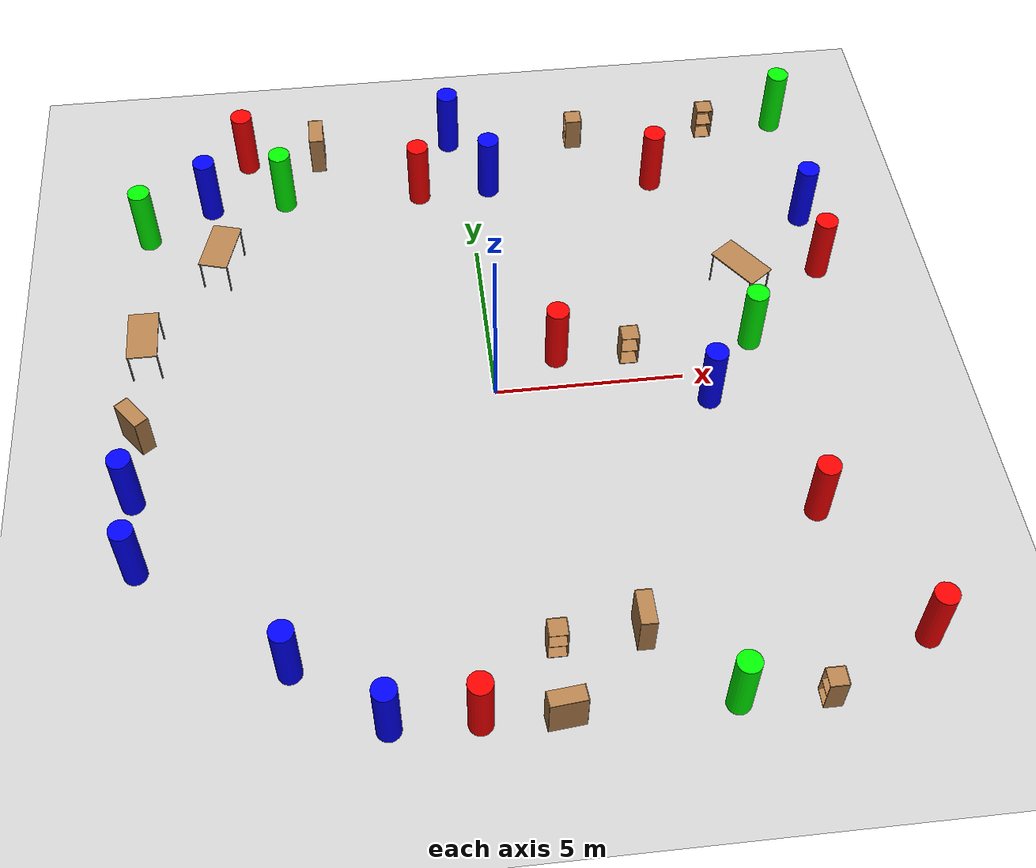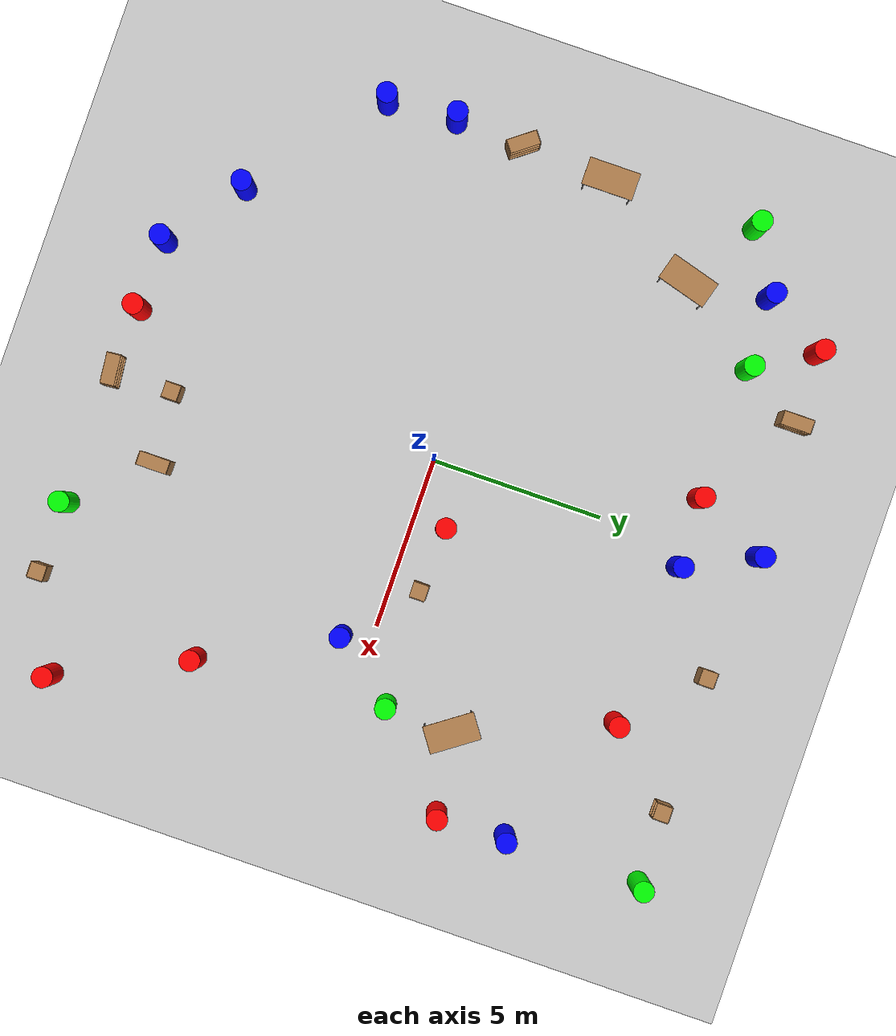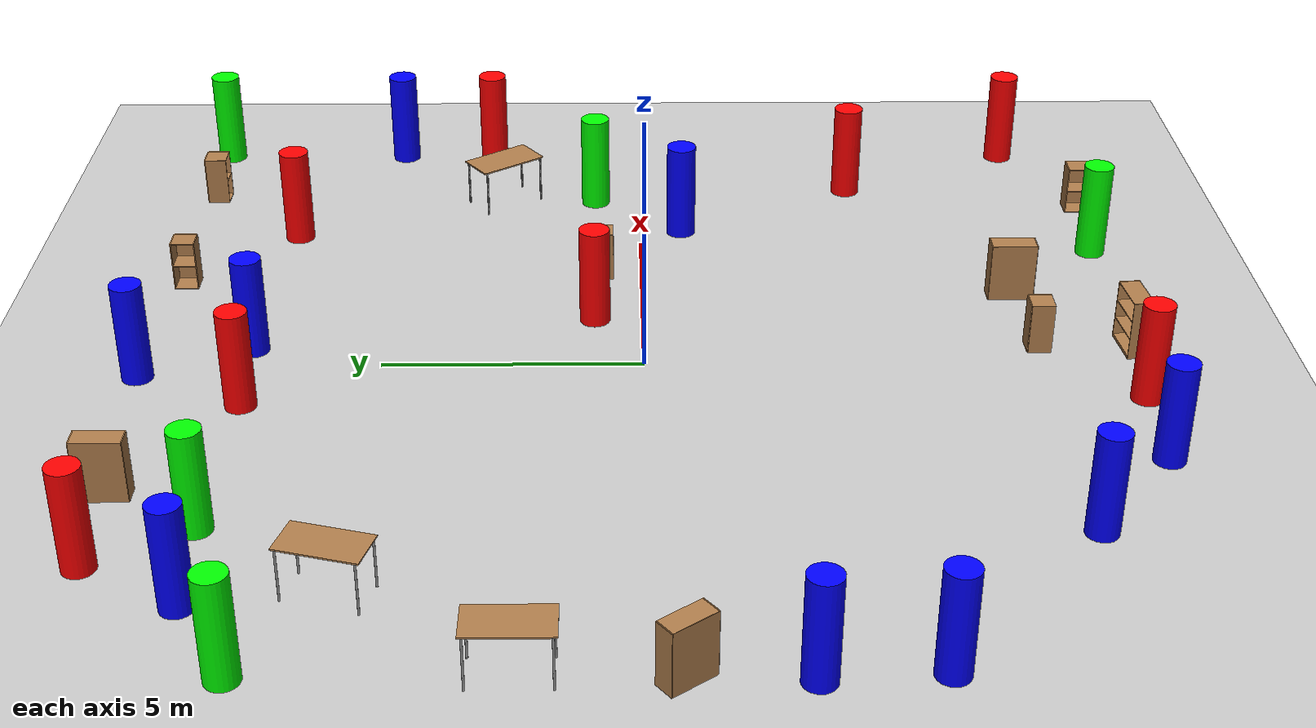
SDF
<sdf version="1.6">
 <world name="default">
  <light name="sun" type="directional">
   <pose>0 0 10 0 -0 0</pose>
   <diffuse>0.8 0.8 0.8 1</diffuse>
   <specular>0.2 0.2 0.2 1</specular>
   <attenuation>
    <range>1000</range>
    <constant>0.9</constant>
    <linear>0.01</linear>
    <quadratic>0.001</quadratic>
   </attenuation>
   <direction>-0.5 0.1 -0.9</direction>
  </light>
  <model name="ground_plane">
   <static>1</static>
   <link name="link">
    <collision name="collision">
     <geometry><plane><normal>0 0 1</normal><size>100 100</size></plane></geometry>
     <surface>
      <contact><collide_bitmask>65535</collide_bitmask></contact>
      <friction><ode><mu>100</mu><mu2>50</mu2></ode></friction>
     </surface>
    </collision>
    <visual name="visual">
     <cast_shadows>0</cast_shadows>
     <geometry><plane><normal>0 0 1</normal><size>100 100</size></plane></geometry>
     <material>
      <script><uri>file://media/materials/scripts/gazebo.material</uri><name>Gazebo/Grey</name></script>
     </material>
    </visual>
   </link>
  </model>
  <gravity>0 0 -9.8</gravity>
  <magnetic_field>6e-06 2.3e-05 -4.2e-05</magnetic_field>
  <atmosphere type="adiabatic"/>
  <physics name="default_physics" default="0" type="ode">
   <max_step_size>0.001</max_step_size>
   <real_time_factor>1</real_time_factor>
   <real_time_update_rate>1000</real_time_update_rate>
  </physics>
  <scene><ambient>0.4 0.4 0.4 1</ambient><background>0.7 0.7 0.7 1</background><shadows>0</shadows></scene>
  <audio><device>default</device></audio>
  <spherical_coordinates>
   <surface_model>EARTH_WGS84</surface_model>
   <latitude_deg>0</latitude_deg>
   <longitude_deg>0</longitude_deg>
   <elevation>0</elevation>
   <heading_deg>0</heading_deg>
  </spherical_coordinates>
  <model name="bookshelf0">
   <static>1</static>
   <link name="link">
    <inertial><mass>1</mass></inertial>
    <collision name="back">
     <pose>0 0.005 0.6 0 -0 0</pose>
     <geometry><box><size>0.9 0.01 1.2</size></box></geometry>
    </collision>
    <visual name="visual1">
     <pose>0 0.005 0.6 0 -0 0</pose>
     <geometry><box><size>0.9 0.01 1.2</size></box></geometry>
     <material>
      <script><uri>file://media/materials/scripts/gazebo.material</uri><name>Gazebo/Wood</name></script>
     </material>
    </visual>
    <collision name="left_side">
     <pose>0.45 -0.195 0.6 0 -0 0</pose>
     <geometry><box><size>0.02 0.4 1.2</size></box></geometry>
    </collision>
    <visual name="visual2">
     <pose>0.45 -0.195 0.6 0 -0 0</pose>
     <geometry><box><size>0.02 0.4 1.2</size></box></geometry>
     <material>
      <script><uri>file://media/materials/scripts/gazebo.material</uri><name>Gazebo/Wood</name></script>
     </material>
    </visual>
    <collision name="right_side">
     <pose>-0.45 -0.195 0.6 0 -0 0</pose>
     <geometry><box><size>0.02 0.4 1.2</size></box></geometry>
    </collision>
    <visual name="visual3">
     <pose>-0.45 -0.195 0.6 0 -0 0</pose>
     <geometry><box><size>0.02 0.4 1.2</size></box></geometry>
     <material>
      <script><uri>file://media/materials/scripts/gazebo.material</uri><name>Gazebo/Wood</name></script>
     </material>
    </visual>
    <collision name="bottom">
     <pose>0 -0.195 0.03 0 -0 0</pose>
     <geometry><box><size>0.88 0.4 0.06</size></box></geometry>
    </collision>
    <visual name="visual4">
     <pose>0 -0.195 0.03 0 -0 0</pose>
     <geometry><box><size>0.88 0.4 0.06</size></box></geometry>
     <material>
      <script><uri>file://media/materials/scripts/gazebo.material</uri><name>Gazebo/Wood</name></script>
     </material>
    </visual>
    <collision name="top">
     <pose>0 -0.195 1.19 0 -0 0</pose>
     <geometry><box><size>0.88 0.4 0.02</size></box></geometry>
    </collision>
    <visual name="visual5">
     <pose>0 -0.195 1.19 0 -0 0</pose>
     <geometry><box><size>0.88 0.4 0.02</size></box></geometry>
     <material>
      <script><uri>file://media/materials/scripts/gazebo.material</uri><name>Gazebo/Wood</name></script>
     </material>
    </visual>
    <collision name="low_shelf">
     <pose>0 -0.195 0.43 0 -0 0</pose>
     <geometry><box><size>0.88 0.4 0.02</size></box></geometry>
    </collision>
    <visual name="visual6">
     <pose>0 -0.195 0.43 0 -0 0</pose>
     <geometry><box><size>0.88 0.4 0.02</size></box></geometry>
     <material>
      <script><uri>file://media/materials/scripts/gazebo.material</uri><name>Gazebo/Wood</name></script>
     </material>
    </visual>
    <collision name="high_shelf">
     <pose>0 -0.195 0.8 0 -0 0</pose>
     <geometry><box><size>0.88 0.4 0.02</size></box></geometry>
    </collision>
    <visual name="visual7">
     <pose>0 -0.195 0.8 0 -0 0</pose>
     <geometry><box><size>0.88 0.4 0.02</size></box></geometry>
     <material>
      <script><uri>file://media/materials/scripts/gazebo.material</uri><name>Gazebo/Wood</name></script>
     </material>
    </visual>
   </link>
   <pose>-9.41642 -0.664219 0 0 -0 2.221</pose>
  </model>
  <model name="bookshelf3">
   <static>1</static>
   <link name="link">
    <inertial><mass>1</mass></inertial>
    <collision name="back">
     <pose>0 0.005 0.6 0 -0 0</pose>
     <geometry><box><size>0.9 0.01 1.2</size></box></geometry>
    </collision>
    <visual name="visual1">
     <pose>0 0.005 0.6 0 -0 0</pose>
     <geometry><box><size>0.9 0.01 1.2</size></box></geometry>
     <material>
      <script><uri>file://media/materials/scripts/gazebo.material</uri><name>Gazebo/Wood</name></script>
     </material>
    </visual>
    <collision name="left_side">
     <pose>0.45 -0.195 0.6 0 -0 0</pose>
     <geometry><box><size>0.02 0.4 1.2</size></box></geometry>
    </collision>
    <visual name="visual2">
     <pose>0.45 -0.195 0.6 0 -0 0</pose>
     <geometry><box><size>0.02 0.4 1.2</size></box></geometry>
     <material>
      <script><uri>file://media/materials/scripts/gazebo.material</uri><name>Gazebo/Wood</name></script>
     </material>
    </visual>
    <collision name="right_side">
     <pose>-0.45 -0.195 0.6 0 -0 0</pose>
     <geometry><box><size>0.02 0.4 1.2</size></box></geometry>
    </collision>
    <visual name="visual3">
     <pose>-0.45 -0.195 0.6 0 -0 0</pose>
     <geometry><box><size>0.02 0.4 1.2</size></box></geometry>
     <material>
      <script><uri>file://media/materials/scripts/gazebo.material</uri><name>Gazebo/Wood</name></script>
     </material>
    </visual>
    <collision name="bottom">
     <pose>0 -0.195 0.03 0 -0 0</pose>
     <geometry><box><size>0.88 0.4 0.06</size></box></geometry>
    </collision>
    <visual name="visual4">
     <pose>0 -0.195 0.03 0 -0 0</pose>
     <geometry><box><size>0.88 0.4 0.06</size></box></geometry>
     <material>
      <script><uri>file://media/materials/scripts/gazebo.material</uri><name>Gazebo/Wood</name></script>
     </material>
    </visual>
    <collision name="top">
     <pose>0 -0.195 1.19 0 -0 0</pose>
     <geometry><box><size>0.88 0.4 0.02</size></box></geometry>
    </collision>
    <visual name="visual5">
     <pose>0 -0.195 1.19 0 -0 0</pose>
     <geometry><box><size>0.88 0.4 0.02</size></box></geometry>
     <material>
      <script><uri>file://media/materials/scripts/gazebo.material</uri><name>Gazebo/Wood</name></script>
     </material>
    </visual>
    <collision name="low_shelf">
     <pose>0 -0.195 0.43 0 -0 0</pose>
     <geometry><box><size>0.88 0.4 0.02</size></box></geometry>
    </collision>
    <visual name="visual6">
     <pose>0 -0.195 0.43 0 -0 0</pose>
     <geometry><box><size>0.88 0.4 0.02</size></box></geometry>
     <material>
      <script><uri>file://media/materials/scripts/gazebo.material</uri><name>Gazebo/Wood</name></script>
     </material>
    </visual>
    <collision name="high_shelf">
     <pose>0 -0.195 0.8 0 -0 0</pose>
     <geometry><box><size>0.88 0.4 0.02</size></box></geometry>
    </collision>
    <visual name="visual7">
     <pose>0 -0.195 0.8 0 -0 0</pose>
     <geometry><box><size>0.88 0.4 0.02</size></box></geometry>
     <material>
      <script><uri>file://media/materials/scripts/gazebo.material</uri><name>Gazebo/Wood</name></script>
     </material>
    </visual>
   </link>
   <pose>0.596082 -9.6045 0 0 0 -3.04017</pose>
  </model>
  <model name="bookshelf4">
   <static>1</static>
   <link name="link">
    <inertial><mass>1</mass></inertial>
    <collision name="back">
     <pose>0 0.005 0.6 0 -0 0</pose>
     <geometry><box><size>0.9 0.01 1.2</size></box></geometry>
    </collision>
    <visual name="visual1">
     <pose>0 0.005 0.6 0 -0 0</pose>
     <geometry><box><size>0.9 0.01 1.2</size></box></geometry>
     <material>
      <script><uri>file://media/materials/scripts/gazebo.material</uri><name>Gazebo/Wood</name></script>
     </material>
    </visual>
    <collision name="left_side">
     <pose>0.45 -0.195 0.6 0 -0 0</pose>
     <geometry><box><size>0.02 0.4 1.2</size></box></geometry>
    </collision>
    <visual name="visual2">
     <pose>0.45 -0.195 0.6 0 -0 0</pose>
     <geometry><box><size>0.02 0.4 1.2</size></box></geometry>
     <material>
      <script><uri>file://media/materials/scripts/gazebo.material</uri><name>Gazebo/Wood</name></script>
     </material>
    </visual>
    <collision name="right_side">
     <pose>-0.45 -0.195 0.6 0 -0 0</pose>
     <geometry><box><size>0.02 0.4 1.2</size></box></geometry>
    </collision>
    <visual name="visual3">
     <pose>-0.45 -0.195 0.6 0 -0 0</pose>
     <geometry><box><size>0.02 0.4 1.2</size></box></geometry>
     <material>
      <script><uri>file://media/materials/scripts/gazebo.material</uri><name>Gazebo/Wood</name></script>
     </material>
    </visual>
    <collision name="bottom">
     <pose>0 -0.195 0.03 0 -0 0</pose>
     <geometry><box><size>0.88 0.4 0.06</size></box></geometry>
    </collision>
    <visual name="visual4">
     <pose>0 -0.195 0.03 0 -0 0</pose>
     <geometry><box><size>0.88 0.4 0.06</size></box></geometry>
     <material>
      <script><uri>file://media/materials/scripts/gazebo.material</uri><name>Gazebo/Wood</name></script>
     </material>
    </visual>
    <collision name="top">
     <pose>0 -0.195 1.19 0 -0 0</pose>
     <geometry><box><size>0.88 0.4 0.02</size></box></geometry>
    </collision>
    <visual name="visual5">
     <pose>0 -0.195 1.19 0 -0 0</pose>
     <geometry><box><size>0.88 0.4 0.02</size></box></geometry>
     <material>
      <script><uri>file://media/materials/scripts/gazebo.material</uri><name>Gazebo/Wood</name></script>
     </material>
    </visual>
    <collision name="low_shelf">
     <pose>0 -0.195 0.43 0 -0 0</pose>
     <geometry><box><size>0.88 0.4 0.02</size></box></geometry>
    </collision>
    <visual name="visual6">
     <pose>0 -0.195 0.43 0 -0 0</pose>
     <geometry><box><size>0.88 0.4 0.02</size></box></geometry>
     <material>
      <script><uri>file://media/materials/scripts/gazebo.material</uri><name>Gazebo/Wood</name></script>
     </material>
    </visual>
    <collision name="high_shelf">
     <pose>0 -0.195 0.8 0 -0 0</pose>
     <geometry><box><size>0.88 0.4 0.02</size></box></geometry>
    </collision>
    <visual name="visual7">
     <pose>0 -0.195 0.8 0 -0 0</pose>
     <geometry><box><size>0.88 0.4 0.02</size></box></geometry>
     <material>
      <script><uri>file://media/materials/scripts/gazebo.material</uri><name>Gazebo/Wood</name></script>
     </material>
    </visual>
   </link>
   <pose>-4.51158 9.29121 0 0 -0 1.5708</pose>
  </model>
  <model name="cabinet0">
   <static>1</static>
   <link name="cabinet_bottom_plate">
    <inertial>
     <pose>0 0 -1 0 -0 0</pose>
     <inertia><ixx>2.05</ixx><ixy>0</ixy><ixz>0</ixz><iyy>2.05</iyy><iyz>0</iyz><izz>2.05</izz></inertia>
     <mass>25</mass>
    </inertial>
    <collision name="cabinet_bottom_plate_geom">
     <pose>0 0 0.01 0 -0 0</pose>
     <geometry><box><size>0.45 0.45 0.02</size></box></geometry>
    </collision>
    <visual name="cabinet_bottom_plate_geom_visual">
     <pose>0 0 0.01 0 -0 0</pose>
     <geometry><box><size>0.45 0.45 0.02</size></box></geometry>
     <material>
      <script><uri>file://media/materials/scripts/gazebo.material</uri><name>Gazebo/Wood</name></script>
     </material>
    </visual>
    <collision name="cabinet_bottom_plate_geom_cabinet_back_plate">
     <pose>0.235 0 0.51 0 -0 0</pose>
     <geometry><box><size>0.02 0.45 1.02</size></box></geometry>
    </collision>
    <visual name="cabinet_bottom_plate_geom_cabinet_back_plate_visual">
     <pose>0.235 0 0.51 0 -0 0</pose>
     <geometry><box><size>0.02 0.45 1.02</size></box></geometry>
     <material>
      <script><uri>file://media/materials/scripts/gazebo.material</uri><name>Gazebo/Wood</name></script>
     </material>
    </visual>
    <collision name="cabinet_bottom_plate_geom_cabinet_left_plate">
     <pose>0 0.235 0.51 0 -0 0</pose>
     <geometry><box><size>0.45 0.02 1.02</size></box></geometry>
    </collision>
    <visual name="cabinet_bottom_plate_geom_cabinet_left_plate_visual">
     <pose>0 0.235 0.51 0 -0 0</pose>
     <geometry><box><size>0.45 0.02 1.02</size></box></geometry>
     <material>
      <script><uri>file://media/materials/scripts/gazebo.material</uri><name>Gazebo/Wood</name></script>
     </material>
    </visual>
    <collision name="cabinet_bottom_plate_geom_cabinet_middle_plate">
     <pose>0 0 0.51 0 -0 0</pose>
     <geometry><box><size>0.45 0.45 0.02</size></box></geometry>
    </collision>
    <visual name="cabinet_bottom_plate_geom_cabinet_middle_plate_visual">
     <pose>0 0 0.51 0 -0 0</pose>
     <geometry><box><size>0.45 0.45 0.02</size></box></geometry>
     <material>
      <script><uri>file://media/materials/scripts/gazebo.material</uri><name>Gazebo/Wood</name></script>
     </material>
    </visual>
    <collision name="cabinet_bottom_plate_geom_cabinet_right_plate">
     <pose>0 -0.235 0.51 0 -0 0</pose>
     <geometry><box><size>0.45 0.02 1.02</size></box></geometry>
    </collision>
    <visual name="cabinet_bottom_plate_geom_cabinet_right_plate_visual">
     <pose>0 -0.235 0.51 0 -0 0</pose>
     <geometry><box><size>0.45 0.02 1.02</size></box></geometry>
     <material>
      <script><uri>file://media/materials/scripts/gazebo.material</uri><name>Gazebo/Wood</name></script>
     </material>
    </visual>
    <collision name="cabinet_bottom_plate_geom_cabinet_top_plate">
     <pose>0 0 1.01 0 -0 0</pose>
     <geometry><box><size>0.45 0.45 0.02</size></box></geometry>
    </collision>
    <visual name="cabinet_bottom_plate_geom_cabinet_top_plate_visual">
     <pose>0 0 1.01 0 -0 0</pose>
     <geometry><box><size>0.45 0.45 0.02</size></box></geometry>
     <material>
      <script><uri>file://media/materials/scripts/gazebo.material</uri><name>Gazebo/Wood</name></script>
     </material>
    </visual>
   </link>
   <pose>3.30482 9.28063 0 0 -0 0</pose>
  </model>
  <model name="cabinet4">
   <static>1</static>
   <link name="cabinet_bottom_plate">
    <inertial>
     <pose>0 0 -1 0 -0 0</pose>
     <inertia><ixx>2.05</ixx><ixy>0</ixy><ixz>0</ixz><iyy>2.05</iyy><iyz>0</iyz><izz>2.05</izz></inertia>
     <mass>25</mass>
    </inertial>
    <collision name="cabinet_bottom_plate_geom">
     <pose>0 0 0.01 0 -0 0</pose>
     <geometry><box><size>0.45 0.45 0.02</size></box></geometry>
    </collision>
    <visual name="cabinet_bottom_plate_geom_visual">
     <pose>0 0 0.01 0 -0 0</pose>
     <geometry><box><size>0.45 0.45 0.02</size></box></geometry>
     <material>
      <script><uri>file://media/materials/scripts/gazebo.material</uri><name>Gazebo/Wood</name></script>
     </material>
    </visual>
    <collision name="cabinet_bottom_plate_geom_cabinet_back_plate">
     <pose>0.235 0 0.51 0 -0 0</pose>
     <geometry><box><size>0.02 0.45 1.02</size></box></geometry>
    </collision>
    <visual name="cabinet_bottom_plate_geom_cabinet_back_plate_visual">
     <pose>0.235 0 0.51 0 -0 0</pose>
     <geometry><box><size>0.02 0.45 1.02</size></box></geometry>
     <material>
      <script><uri>file://media/materials/scripts/gazebo.material</uri><name>Gazebo/Wood</name></script>
     </material>
    </visual>
    <collision name="cabinet_bottom_plate_geom_cabinet_left_plate">
     <pose>0 0.235 0.51 0 -0 0</pose>
     <geometry><box><size>0.45 0.02 1.02</size></box></geometry>
    </collision>
    <visual name="cabinet_bottom_plate_geom_cabinet_left_plate_visual">
     <pose>0 0.235 0.51 0 -0 0</pose>
     <geometry><box><size>0.45 0.02 1.02</size></box></geometry>
     <material>
      <script><uri>file://media/materials/scripts/gazebo.material</uri><name>Gazebo/Wood</name></script>
     </material>
    </visual>
    <collision name="cabinet_bottom_plate_geom_cabinet_middle_plate">
     <pose>0 0 0.51 0 -0 0</pose>
     <geometry><box><size>0.45 0.45 0.02</size></box></geometry>
    </collision>
    <visual name="cabinet_bottom_plate_geom_cabinet_middle_plate_visual">
     <pose>0 0 0.51 0 -0 0</pose>
     <geometry><box><size>0.45 0.45 0.02</size></box></geometry>
     <material>
      <script><uri>file://media/materials/scripts/gazebo.material</uri><name>Gazebo/Wood</name></script>
     </material>
    </visual>
    <collision name="cabinet_bottom_plate_geom_cabinet_right_plate">
     <pose>0 -0.235 0.51 0 -0 0</pose>
     <geometry><box><size>0.45 0.02 1.02</size></box></geometry>
    </collision>
    <visual name="cabinet_bottom_plate_geom_cabinet_right_plate_visual">
     <pose>0 -0.235 0.51 0 -0 0</pose>
     <geometry><box><size>0.45 0.02 1.02</size></box></geometry>
     <material>
      <script><uri>file://media/materials/scripts/gazebo.material</uri><name>Gazebo/Wood</name></script>
     </material>
    </visual>
    <collision name="cabinet_bottom_plate_geom_cabinet_top_plate">
     <pose>0 0 1.01 0 -0 0</pose>
     <geometry><box><size>0.45 0.45 0.02</size></box></geometry>
    </collision>
    <visual name="cabinet_bottom_plate_geom_cabinet_top_plate_visual">
     <pose>0 0 1.01 0 -0 0</pose>
     <geometry><box><size>0.45 0.45 0.02</size></box></geometry>
     <material>
      <script><uri>file://media/materials/scripts/gazebo.material</uri><name>Gazebo/Wood</name></script>
     </material>
    </visual>
   </link>
   <pose>7.28077 9.29854 0 0 -0 1.5708</pose>
  </model>
  <model name="table1">
   <static>1</static>
   <link name="link">
    <collision name="surface">
     <pose>0 0 1 0 -0 0</pose>
     <geometry><box><size>1.5 0.8 0.03</size></box></geometry>
     <surface><friction><ode><mu>0.6</mu><mu2>0.6</mu2></ode></friction></surface>
    </collision>
    <visual name="visual1">
     <pose>0 0 1 0 -0 0</pose>
     <geometry><box><size>1.5 0.8 0.03</size></box></geometry>
     <material>
      <script><uri>file://media/materials/scripts/gazebo.material</uri><name>Gazebo/Wood</name></script>
     </material>
    </visual>
    <collision name="front_left_leg">
     <pose>0.68 0.38 0.5 0 -0 0</pose>
     <geometry><cylinder><radius>0.02</radius><length>1</length></cylinder></geometry>
    </collision>
    <visual name="front_left_leg">
     <pose>0.68 0.38 0.5 0 -0 0</pose>
     <geometry><cylinder><radius>0.02</radius><length>1</length></cylinder></geometry>
     <material>
      <script><uri>file://media/materials/scripts/gazebo.material</uri><name>Gazebo/Grey</name></script>
     </material>
    </visual>
    <collision name="front_right_leg">
     <pose>0.68 -0.38 0.5 0 -0 0</pose>
     <geometry><cylinder><radius>0.02</radius><length>1</length></cylinder></geometry>
    </collision>
    <visual name="front_right_leg">
     <pose>0.68 -0.38 0.5 0 -0 0</pose>
     <geometry><cylinder><radius>0.02</radius><length>1</length></cylinder></geometry>
     <material>
      <script><uri>file://media/materials/scripts/gazebo.material</uri><name>Gazebo/Grey</name></script>
     </material>
    </visual>
    <collision name="back_right_leg">
     <pose>-0.68 -0.38 0.5 0 -0 0</pose>
     <geometry><cylinder><radius>0.02</radius><length>1</length></cylinder></geometry>
    </collision>
    <visual name="back_right_leg">
     <pose>-0.68 -0.38 0.5 0 -0 0</pose>
     <geometry><cylinder><radius>0.02</radius><length>1</length></cylinder></geometry>
     <material>
      <script><uri>file://media/materials/scripts/gazebo.material</uri><name>Gazebo/Grey</name></script>
     </material>
    </visual>
    <collision name="back_left_leg">
     <pose>-0.68 0.38 0.5 0 -0 0</pose>
     <geometry><cylinder><radius>0.02</radius><length>1</length></cylinder></geometry>
    </collision>
    <visual name="back_left_leg">
     <pose>-0.68 0.38 0.5 0 -0 0</pose>
     <geometry><cylinder><radius>0.02</radius><length>1</length></cylinder></geometry>
     <material>
      <script><uri>file://media/materials/scripts/gazebo.material</uri><name>Gazebo/Grey</name></script>
     </material>
    </visual>
   </link>
   <pose>-9.1077 2.12163 0 0 0 -1.5708</pose>
  </model>
  <model name="table2">
   <static>1</static>
   <link name="link">
    <collision name="surface">
     <pose>0 0 1 0 -0 0</pose>
     <geometry><box><size>1.5 0.8 0.03</size></box></geometry>
     <surface><friction><ode><mu>0.6</mu><mu2>0.6</mu2></ode></friction></surface>
    </collision>
    <visual name="visual1">
     <pose>0 0 1 0 -0 0</pose>
     <geometry><box><size>1.5 0.8 0.03</size></box></geometry>
     <material>
      <script><uri>file://media/materials/scripts/gazebo.material</uri><name>Gazebo/Wood</name></script>
     </material>
    </visual>
    <collision name="front_left_leg">
     <pose>0.68 0.38 0.5 0 -0 0</pose>
     <geometry><cylinder><radius>0.02</radius><length>1</length></cylinder></geometry>
    </collision>
    <visual name="front_left_leg">
     <pose>0.68 0.38 0.5 0 -0 0</pose>
     <geometry><cylinder><radius>0.02</radius><length>1</length></cylinder></geometry>
     <material>
      <script><uri>file://media/materials/scripts/gazebo.material</uri><name>Gazebo/Grey</name></script>
     </material>
    </visual>
    <collision name="front_right_leg">
     <pose>0.68 -0.38 0.5 0 -0 0</pose>
     <geometry><cylinder><radius>0.02</radius><length>1</length></cylinder></geometry>
    </collision>
    <visual name="front_right_leg">
     <pose>0.68 -0.38 0.5 0 -0 0</pose>
     <geometry><cylinder><radius>0.02</radius><length>1</length></cylinder></geometry>
     <material>
      <script><uri>file://media/materials/scripts/gazebo.material</uri><name>Gazebo/Grey</name></script>
     </material>
    </visual>
    <collision name="back_right_leg">
     <pose>-0.68 -0.38 0.5 0 -0 0</pose>
     <geometry><cylinder><radius>0.02</radius><length>1</length></cylinder></geometry>
    </collision>
    <visual name="back_right_leg">
     <pose>-0.68 -0.38 0.5 0 -0 0</pose>
     <geometry><cylinder><radius>0.02</radius><length>1</length></cylinder></geometry>
     <material>
      <script><uri>file://media/materials/scripts/gazebo.material</uri><name>Gazebo/Grey</name></script>
     </material>
    </visual>
    <collision name="back_left_leg">
     <pose>-0.68 0.38 0.5 0 -0 0</pose>
     <geometry><cylinder><radius>0.02</radius><length>1</length></cylinder></geometry>
    </collision>
    <visual name="back_left_leg">
     <pose>-0.68 0.38 0.5 0 -0 0</pose>
     <geometry><cylinder><radius>0.02</radius><length>1</length></cylinder></geometry>
     <material>
      <script><uri>file://media/materials/scripts/gazebo.material</uri><name>Gazebo/Grey</name></script>
     </material>
    </visual>
   </link>
   <pose>7.0955 2.98202 0 0 -0 2.19088</pose>
  </model>
  <model name="red0">
   <link name="link">
    <pose>-0.202221 0.506091 0 0 -0 0</pose>
    <inertial>
     <mass>1</mass>
     <inertia><ixx>0.145833</ixx><ixy>0</ixy><ixz>0</ixz><iyy>0.145833</iyy><iyz>0</iyz><izz>0.125</izz></inertia>
    </inertial>
    <visual name="visual">
     <geometry><cylinder><radius>0.3</radius><length>2</length></cylinder></geometry>
     <material>
      <script><name>Gazebo/Grey</name><uri>file://media/materials/scripts/gazebo.material</uri></script>
      <ambient>1 0 0 1</ambient>
      <diffuse>0.7 0.7 0.7 1</diffuse>
      <specular>0.01 0.01 0.01 1</specular>
      <emissive>0 0 0 1</emissive>
      <shader type="vertex"><normal_map>__default__</normal_map></shader>
     </material>
    </visual>
    <collision name="collision">
     <geometry><cylinder><radius>0.3</radius><length>2</length></cylinder></geometry>
     <surface>
      <friction>
       <ode><mu>1</mu><mu2>1</mu2><fdir1>0 0 0</fdir1><slip1>0</slip1><slip2>0</slip2></ode>
       <torsional>
        <coefficient>1</coefficient>
        <patch_radius>0</patch_radius>
        <surface_radius>0</surface_radius>
        <use_patch_radius>1</use_patch_radius>
        <ode><slip>0</slip></ode>
       </torsional>
      </friction>
      <bounce><restitution_coefficient>0</restitution_coefficient><threshold>1e+06</threshold></bounce>
      <contact>
       <collide_without_contact>0</collide_without_contact>
       <collide_without_contact_bitmask>1</collide_without_contact_bitmask>
       <collide_bitmask>1</collide_bitmask>
       <ode>
        <soft_cfm>0</soft_cfm>
        <soft_erp>0.2</soft_erp>
        <kp>1e+13</kp>
        <kd>1</kd>
        <max_vel>0.01</max_vel>
        <min_depth>0</min_depth>
       </ode>
       <bullet>
        <split_impulse>1</split_impulse>
        <split_impulse_penetration_threshold>-0.01</split_impulse_penetration_threshold>
        <soft_cfm>0</soft_cfm>
        <soft_erp>0.2</soft_erp>
        <kp>1e+13</kp>
        <kd>1</kd>
       </bullet>
      </contact>
     </surface>
    </collision>
   </link>
   <static>0</static>
   <pose>-6.19458 8.75099 0.999992 0 -0 9.3e-05</pose>
  </model>
  <model name="red3">
   <link name="link">
    <pose>-0.202221 0.506091 0 0 -0 0</pose>
    <inertial>
     <mass>1</mass>
     <inertia><ixx>0.145833</ixx><ixy>0</ixy><ixz>0</ixz><iyy>0.145833</iyy><iyz>0</iyz><izz>0.125</izz></inertia>
    </inertial>
    <visual name="visual">
     <geometry><cylinder><radius>0.3</radius><length>2</length></cylinder></geometry>
     <material>
      <script><name>Gazebo/Grey</name><uri>file://media/materials/scripts/gazebo.material</uri></script>
      <ambient>1 0 0 1</ambient>
      <diffuse>0.7 0.7 0.7 1</diffuse>
      <specular>0.01 0.01 0.01 1</specular>
      <emissive>0 0 0 1</emissive>
      <shader type="vertex"><normal_map>__default__</normal_map></shader>
     </material>
    </visual>
    <collision name="collision">
     <geometry><cylinder><radius>0.3</radius><length>2</length></cylinder></geometry>
     <surface>
      <friction>
       <ode><mu>1</mu><mu2>1</mu2><fdir1>0 0 0</fdir1><slip1>0</slip1><slip2>0</slip2></ode>
       <torsional>
        <coefficient>1</coefficient>
        <patch_radius>0</patch_radius>
        <surface_radius>0</surface_radius>
        <use_patch_radius>1</use_patch_radius>
        <ode><slip>0</slip></ode>
       </torsional>
      </friction>
      <bounce><restitution_coefficient>0</restitution_coefficient><threshold>1e+06</threshold></bounce>
      <contact>
       <collide_without_contact>0</collide_without_contact>
       <collide_without_contact_bitmask>1</collide_without_contact_bitmask>
       <collide_bitmask>1</collide_bitmask>
       <ode>
        <soft_cfm>0</soft_cfm>
        <soft_erp>0.2</soft_erp>
        <kp>1e+13</kp>
        <kd>1</kd>
        <max_vel>0.01</max_vel>
        <min_depth>0</min_depth>
       </ode>
       <bullet>
        <split_impulse>1</split_impulse>
        <split_impulse_penetration_threshold>-0.01</split_impulse_penetration_threshold>
        <soft_cfm>0</soft_cfm>
        <soft_erp>0.2</soft_erp>
        <kp>1e+13</kp>
        <kd>1</kd>
       </bullet>
      </contact>
     </surface>
    </collision>
   </link>
   <static>0</static>
   <pose>-1.12177 -9.80828 0.999991 0 -0 4.9e-05</pose>
  </model>
  <model name="red5">
   <link name="link">
    <pose>-0.202221 0.506091 0 0 -0 0</pose>
    <inertial>
     <mass>1</mass>
     <inertia><ixx>0.145833</ixx><ixy>0</ixy><ixz>0</ixz><iyy>0.145833</iyy><iyz>0</iyz><izz>0.125</izz></inertia>
    </inertial>
    <visual name="visual">
     <geometry><cylinder><radius>0.3</radius><length>2</length></cylinder></geometry>
     <material>
      <script><name>Gazebo/Grey</name><uri>file://media/materials/scripts/gazebo.material</uri></script>
      <ambient>1 0 0 1</ambient>
      <diffuse>0.7 0.7 0.7 1</diffuse>
      <specular>0.01 0.01 0.01 1</specular>
      <emissive>0 0 0 1</emissive>
      <shader type="vertex"><normal_map>__default__</normal_map></shader>
     </material>
    </visual>
    <collision name="collision">
     <geometry><cylinder><radius>0.3</radius><length>2</length></cylinder></geometry>
     <surface>
      <friction>
       <ode><mu>1</mu><mu2>1</mu2><fdir1>0 0 0</fdir1><slip1>0</slip1><slip2>0</slip2></ode>
       <torsional>
        <coefficient>1</coefficient>
        <patch_radius>0</patch_radius>
        <surface_radius>0</surface_radius>
        <use_patch_radius>1</use_patch_radius>
        <ode><slip>0</slip></ode>
       </torsional>
      </friction>
      <bounce><restitution_coefficient>0</restitution_coefficient><threshold>1e+06</threshold></bounce>
      <contact>
       <collide_without_contact>0</collide_without_contact>
       <collide_without_contact_bitmask>1</collide_without_contact_bitmask>
       <collide_bitmask>1</collide_bitmask>
       <ode>
        <soft_cfm>0</soft_cfm>
        <soft_erp>0.2</soft_erp>
        <kp>1e+13</kp>
        <kd>1</kd>
        <max_vel>0.01</max_vel>
        <min_depth>0</min_depth>
       </ode>
       <bullet>
        <split_impulse>1</split_impulse>
        <split_impulse_penetration_threshold>-0.01</split_impulse_penetration_threshold>
        <soft_cfm>0</soft_cfm>
        <soft_erp>0.2</soft_erp>
        <kp>1e+13</kp>
        <kd>1</kd>
       </bullet>
      </contact>
     </surface>
    </collision>
   </link>
   <static>0</static>
   <pose>9.62587 2.83361 0.999993 0 -0 5.3e-05</pose>
  </model>
  <model name="green4">
   <link name="link">
    <inertial>
     <mass>1</mass>
     <inertia><ixx>0.145833</ixx><ixy>0</ixy><ixz>0</ixz><iyy>0.145833</iyy><iyz>0</iyz><izz>0.125</izz></inertia>
    </inertial>
    <visual name="visual">
     <geometry><cylinder><radius>0.3</radius><length>2</length></cylinder></geometry>
     <material>
      <script><name>Gazebo/Grey</name><uri>file://media/materials/scripts/gazebo.material</uri></script>
      <ambient>0 1 0 1</ambient>
      <diffuse>0.7 0.7 0.7 1</diffuse>
      <specular>0.01 0.01 0.01 1</specular>
      <emissive>0 0 0 1</emissive>
      <shader type="vertex"><normal_map>__default__</normal_map></shader>
     </material>
    </visual>
    <collision name="collision">
     <geometry><cylinder><radius>0.3</radius><length>2</length></cylinder></geometry>
     <surface>
      <friction>
       <ode><mu>1</mu><mu2>1</mu2><fdir1>0 0 0</fdir1><slip1>0</slip1><slip2>0</slip2></ode>
       <torsional>
        <coefficient>1</coefficient>
        <patch_radius>0</patch_radius>
        <surface_radius>0</surface_radius>
        <use_patch_radius>1</use_patch_radius>
        <ode><slip>0</slip></ode>
       </torsional>
      </friction>
      <bounce><restitution_coefficient>0</restitution_coefficient><threshold>1e+06</threshold></bounce>
      <contact>
       <collide_without_contact>0</collide_without_contact>
       <collide_without_contact_bitmask>1</collide_without_contact_bitmask>
       <collide_bitmask>1</collide_bitmask>
       <ode>
        <soft_cfm>0</soft_cfm>
        <soft_erp>0.2</soft_erp>
        <kp>1e+13</kp>
        <kd>1</kd>
        <max_vel>0.01</max_vel>
        <min_depth>0</min_depth>
       </ode>
       <bullet>
        <split_impulse>1</split_impulse>
        <split_impulse_penetration_threshold>-0.01</split_impulse_penetration_threshold>
        <soft_cfm>0</soft_cfm>
        <soft_erp>0.2</soft_erp>
        <kp>1e+13</kp>
        <kd>1</kd>
       </bullet>
      </contact>
     </surface>
    </collision>
   </link>
   <static>0</static>
   <pose>-9.21307 6.44775 0.999999 0 -0 9.8e-05</pose>
  </model>
  <model name="green6">
   <link name="link">
    <inertial>
     <mass>1</mass>
     <inertia><ixx>0.145833</ixx><ixy>0</ixy><ixz>0</ixz><iyy>0.145833</iyy><iyz>0</iyz><izz>0.125</izz></inertia>
    </inertial>
    <visual name="visual">
     <geometry><cylinder><radius>0.3</radius><length>2</length></cylinder></geometry>
     <material>
      <script><name>Gazebo/Grey</name><uri>file://media/materials/scripts/gazebo.material</uri></script>
      <ambient>0 1 0 1</ambient>
      <diffuse>0.7 0.7 0.7 1</diffuse>
      <specular>0.01 0.01 0.01 1</specular>
      <emissive>0 0 0 1</emissive>
      <shader type="vertex"><normal_map>__default__</normal_map></shader>
     </material>
    </visual>
    <collision name="collision">
     <geometry><cylinder><radius>0.3</radius><length>2</length></cylinder></geometry>
     <surface>
      <friction>
       <ode><mu>1</mu><mu2>1</mu2><fdir1>0 0 0</fdir1><slip1>0</slip1><slip2>0</slip2></ode>
       <torsional>
        <coefficient>1</coefficient>
        <patch_radius>0</patch_radius>
        <surface_radius>0</surface_radius>
        <use_patch_radius>1</use_patch_radius>
        <ode><slip>0</slip></ode>
       </torsional>
      </friction>
      <bounce><restitution_coefficient>0</restitution_coefficient><threshold>1e+06</threshold></bounce>
      <contact>
       <collide_without_contact>0</collide_without_contact>
       <collide_without_contact_bitmask>1</collide_without_contact_bitmask>
       <collide_bitmask>1</collide_bitmask>
       <ode>
        <soft_cfm>0</soft_cfm>
        <soft_erp>0.2</soft_erp>
        <kp>1e+13</kp>
        <kd>1</kd>
        <max_vel>0.01</max_vel>
        <min_depth>0</min_depth>
       </ode>
       <bullet>
        <split_impulse>1</split_impulse>
        <split_impulse_penetration_threshold>-0.01</split_impulse_penetration_threshold>
        <soft_cfm>0</soft_cfm>
        <soft_erp>0.2</soft_erp>
        <kp>1e+13</kp>
        <kd>1</kd>
       </bullet>
      </contact>
     </surface>
    </collision>
   </link>
   <static>0</static>
   <pose>9.42652 9.38493 0.999993 0 -0 1.57251</pose>
  </model>
  <model name="blue0">
   <link name="link">
    <inertial>
     <mass>1</mass>
     <inertia><ixx>0.145833</ixx><ixy>0</ixy><ixz>0</ixz><iyy>0.145833</iyy><iyz>0</iyz><izz>0.125</izz></inertia>
    </inertial>
    <visual name="visual">
     <geometry><cylinder><radius>0.3</radius><length>2</length></cylinder></geometry>
     <material>
      <script><name>Gazebo/Grey</name><uri>file://media/materials/scripts/gazebo.material</uri></script>
      <ambient>0 0 1 1</ambient>
      <diffuse>0.7 0.7 0.7 1</diffuse>
      <specular>0.01 0.01 0.01 1</specular>
      <emissive>0 0 0 1</emissive>
      <shader type="vertex"><normal_map>__default__</normal_map></shader>
     </material>
    </visual>
    <collision name="collision">
     <geometry><cylinder><radius>0.2</radius><length>2</length></cylinder></geometry>
     <surface>
      <friction>
       <ode><mu>1</mu><mu2>1</mu2><fdir1>0 0 0</fdir1><slip1>0</slip1><slip2>0</slip2></ode>
       <torsional>
        <coefficient>1</coefficient>
        <patch_radius>0</patch_radius>
        <surface_radius>0</surface_radius>
        <use_patch_radius>1</use_patch_radius>
        <ode><slip>0</slip></ode>
       </torsional>
      </friction>
      <bounce><restitution_coefficient>0</restitution_coefficient><threshold>1e+06</threshold></bounce>
      <contact>
       <collide_without_contact>0</collide_without_contact>
       <collide_without_contact_bitmask>1</collide_without_contact_bitmask>
       <collide_bitmask>1</collide_bitmask>
       <ode>
        <soft_cfm>0</soft_cfm>
        <soft_erp>0.2</soft_erp>
        <kp>1e+13</kp>
        <kd>1</kd>
        <max_vel>0.01</max_vel>
        <min_depth>0</min_depth>
       </ode>
       <bullet>
        <split_impulse>1</split_impulse>
        <split_impulse_penetration_threshold>-0.01</split_impulse_penetration_threshold>
        <soft_cfm>0</soft_cfm>
        <soft_erp>0.2</soft_erp>
        <kp>1e+13</kp>
        <kd>1</kd>
       </bullet>
      </contact>
     </surface>
    </collision>
   </link>
   <static>0</static>
   <pose>-3.38855 -9.22957 0.999996 0 0 -0.011931</pose>
  </model>
  <model name="blue1">
   <link name="link">
    <inertial>
     <mass>1</mass>
     <inertia><ixx>0.145833</ixx><ixy>0</ixy><ixz>0</ixz><iyy>0.145833</iyy><iyz>0</iyz><izz>0.125</izz></inertia>
    </inertial>
    <visual name="visual">
     <geometry><cylinder><radius>0.3</radius><length>2</length></cylinder></geometry>
     <material>
      <script><name>Gazebo/Grey</name><uri>file://media/materials/scripts/gazebo.material</uri></script>
      <ambient>0 0 1 1</ambient>
      <diffuse>0.7 0.7 0.7 1</diffuse>
      <specular>0.01 0.01 0.01 1</specular>
      <emissive>0 0 0 1</emissive>
      <shader type="vertex"><normal_map>__default__</normal_map></shader>
     </material>
    </visual>
    <collision name="collision">
     <geometry><cylinder><radius>0.2</radius><length>2</length></cylinder></geometry>
     <surface>
      <friction>
       <ode><mu>1</mu><mu2>1</mu2><fdir1>0 0 0</fdir1><slip1>0</slip1><slip2>0</slip2></ode>
       <torsional>
        <coefficient>1</coefficient>
        <patch_radius>0</patch_radius>
        <surface_radius>0</surface_radius>
        <use_patch_radius>1</use_patch_radius>
        <ode><slip>0</slip></ode>
       </torsional>
      </friction>
      <bounce><restitution_coefficient>0</restitution_coefficient><threshold>1e+06</threshold></bounce>
      <contact>
       <collide_without_contact>0</collide_without_contact>
       <collide_without_contact_bitmask>1</collide_without_contact_bitmask>
       <collide_bitmask>1</collide_bitmask>
       <ode>
        <soft_cfm>0</soft_cfm>
        <soft_erp>0.2</soft_erp>
        <kp>1e+13</kp>
        <kd>1</kd>
        <max_vel>0.01</max_vel>
        <min_depth>0</min_depth>
       </ode>
       <bullet>
        <split_impulse>1</split_impulse>
        <split_impulse_penetration_threshold>-0.01</split_impulse_penetration_threshold>
        <soft_cfm>0</soft_cfm>
        <soft_erp>0.2</soft_erp>
        <kp>1e+13</kp>
        <kd>1</kd>
       </bullet>
      </contact>
     </surface>
    </collision>
   </link>
   <static>0</static>
   <pose>9.39957 5.36753 0.999996 0 0 -0.007206</pose>
  </model>
  <model name="blue3">
   <link name="link">
    <inertial>
     <mass>1</mass>
     <inertia><ixx>0.145833</ixx><ixy>0</ixy><ixz>0</ixz><iyy>0.145833</iyy><iyz>0</iyz><izz>0.125</izz></inertia>
    </inertial>
    <visual name="visual">
     <geometry><cylinder><radius>0.3</radius><length>2</length></cylinder></geometry>
     <material>
      <script><name>Gazebo/Grey</name><uri>file://media/materials/scripts/gazebo.material</uri></script>
      <ambient>0 0 1 1</ambient>
      <diffuse>0.7 0.7 0.7 1</diffuse>
      <specular>0.01 0.01 0.01 1</specular>
      <emissive>0 0 0 1</emissive>
      <shader type="vertex"><normal_map>__default__</normal_map></shader>
     </material>
    </visual>
    <collision name="collision">
     <geometry><cylinder><radius>0.2</radius><length>2</length></cylinder></geometry>
     <surface>
      <friction>
       <ode><mu>1</mu><mu2>1</mu2><fdir1>0 0 0</fdir1><slip1>0</slip1><slip2>0</slip2></ode>
       <torsional>
        <coefficient>1</coefficient>
        <patch_radius>0</patch_radius>
        <surface_radius>0</surface_radius>
        <use_patch_radius>1</use_patch_radius>
        <ode><slip>0</slip></ode>
       </torsional>
      </friction>
      <bounce><restitution_coefficient>0</restitution_coefficient><threshold>1e+06</threshold></bounce>
      <contact>
       <collide_without_contact>0</collide_without_contact>
       <collide_without_contact_bitmask>1</collide_without_contact_bitmask>
       <collide_bitmask>1</collide_bitmask>
       <ode>
        <soft_cfm>0</soft_cfm>
        <soft_erp>0.2</soft_erp>
        <kp>1e+13</kp>
        <kd>1</kd>
        <max_vel>0.01</max_vel>
        <min_depth>0</min_depth>
       </ode>
       <bullet>
        <split_impulse>1</split_impulse>
        <split_impulse_penetration_threshold>-0.01</split_impulse_penetration_threshold>
        <soft_cfm>0</soft_cfm>
        <soft_erp>0.2</soft_erp>
        <kp>1e+13</kp>
        <kd>1</kd>
       </bullet>
      </contact>
     </surface>
    </collision>
   </link>
   <static>0</static>
   <pose>-9.32981 -2.54026 1 0 0 -0.009931</pose>
  </model>
  <model name="blue4">
   <link name="link">
    <inertial>
     <mass>1</mass>
     <inertia><ixx>0.145833</ixx><ixy>0</ixy><ixz>0</ixz><iyy>0.145833</iyy><iyz>0</iyz><izz>0.125</izz></inertia>
    </inertial>
    <visual name="visual">
     <geometry><cylinder><radius>0.3</radius><length>2</length></cylinder></geometry>
     <material>
      <script><name>Gazebo/Grey</name><uri>file://media/materials/scripts/gazebo.material</uri></script>
      <ambient>0 0 1 1</ambient>
      <diffuse>0.7 0.7 0.7 1</diffuse>
      <specular>0.01 0.01 0.01 1</specular>
      <emissive>0 0 0 1</emissive>
      <shader type="vertex"><normal_map>__default__</normal_map></shader>
     </material>
    </visual>
    <collision name="collision">
     <geometry><cylinder><radius>0.2</radius><length>2</length></cylinder></geometry>
     <surface>
      <friction>
       <ode><mu>1</mu><mu2>1</mu2><fdir1>0 0 0</fdir1><slip1>0</slip1><slip2>0</slip2></ode>
       <torsional>
        <coefficient>1</coefficient>
        <patch_radius>0</patch_radius>
        <surface_radius>0</surface_radius>
        <use_patch_radius>1</use_patch_radius>
        <ode><slip>0</slip></ode>
       </torsional>
      </friction>
      <bounce><restitution_coefficient>0</restitution_coefficient><threshold>1e+06</threshold></bounce>
      <contact>
       <collide_without_contact>0</collide_without_contact>
       <collide_without_contact_bitmask>1</collide_without_contact_bitmask>
       <collide_bitmask>1</collide_bitmask>
       <ode>
        <soft_cfm>0</soft_cfm>
        <soft_erp>0.2</soft_erp>
        <kp>1e+13</kp>
        <kd>1</kd>
        <max_vel>0.01</max_vel>
        <min_depth>0</min_depth>
       </ode>
       <bullet>
        <split_impulse>1</split_impulse>
        <split_impulse_penetration_threshold>-0.01</split_impulse_penetration_threshold>
        <soft_cfm>0</soft_cfm>
        <soft_erp>0.2</soft_erp>
        <kp>1e+13</kp>
        <kd>1</kd>
       </bullet>
      </contact>
     </surface>
    </collision>
   </link>
   <static>0</static>
   <pose>-9.18518 -4.56966 1 0 0 -0.010988</pose>
  </model>
  <model name="blue5">
   <link name="link">
    <inertial>
     <mass>1</mass>
     <inertia><ixx>0.145833</ixx><ixy>0</ixy><ixz>0</ixz><iyy>0.145833</iyy><iyz>0</iyz><izz>0.125</izz></inertia>
    </inertial>
    <visual name="visual">
     <geometry><cylinder><radius>0.3</radius><length>2</length></cylinder></geometry>
     <material>
      <script><name>Gazebo/Grey</name><uri>file://media/materials/scripts/gazebo.material</uri></script>
      <ambient>0 0 1 1</ambient>
      <diffuse>0.7 0.7 0.7 1</diffuse>
      <specular>0.01 0.01 0.01 1</specular>
      <emissive>0 0 0 1</emissive>
      <shader type="vertex"><normal_map>__default__</normal_map></shader>
     </material>
    </visual>
    <collision name="collision">
     <geometry><cylinder><radius>0.2</radius><length>2</length></cylinder></geometry>
     <surface>
      <friction>
       <ode><mu>1</mu><mu2>1</mu2><fdir1>0 0 0</fdir1><slip1>0</slip1><slip2>0</slip2></ode>
       <torsional>
        <coefficient>1</coefficient>
        <patch_radius>0</patch_radius>
        <surface_radius>0</surface_radius>
        <use_patch_radius>1</use_patch_radius>
        <ode><slip>0</slip></ode>
       </torsional>
      </friction>
      <bounce><restitution_coefficient>0</restitution_coefficient><threshold>1e+06</threshold></bounce>
      <contact>
       <collide_without_contact>0</collide_without_contact>
       <collide_without_contact_bitmask>1</collide_without_contact_bitmask>
       <collide_bitmask>1</collide_bitmask>
       <ode>
        <soft_cfm>0</soft_cfm>
        <soft_erp>0.2</soft_erp>
        <kp>1e+13</kp>
        <kd>1</kd>
        <max_vel>0.01</max_vel>
        <min_depth>0</min_depth>
       </ode>
       <bullet>
        <split_impulse>1</split_impulse>
        <split_impulse_penetration_threshold>-0.01</split_impulse_penetration_threshold>
        <soft_cfm>0</soft_cfm>
        <soft_erp>0.2</soft_erp>
        <kp>1e+13</kp>
        <kd>1</kd>
       </bullet>
      </contact>
     </surface>
    </collision>
   </link>
   <static>0</static>
   <pose>-0.40548 9.5525 0.999996 0 0 -0.005155</pose>
  </model>
  <model name="cabinet0_clone">
   <static>1</static>
   <link name="cabinet_bottom_plate">
    <inertial>
     <pose>0 0 -1 0 -0 0</pose>
     <inertia><ixx>2.05</ixx><ixy>0</ixy><ixz>0</ixz><iyy>2.05</iyy><iyz>0</iyz><izz>2.05</izz></inertia>
     <mass>25</mass>
    </inertial>
    <collision name="cabinet_bottom_plate_geom">
     <pose>0 0 0.01 0 -0 0</pose>
     <geometry><box><size>0.45 0.45 0.02</size></box></geometry>
    </collision>
    <visual name="cabinet_bottom_plate_geom_visual">
     <pose>0 0 0.01 0 -0 0</pose>
     <geometry><box><size>0.45 0.45 0.02</size></box></geometry>
     <material>
      <script><uri>file://media/materials/scripts/gazebo.material</uri><name>Gazebo/Wood</name></script>
     </material>
    </visual>
    <collision name="cabinet_bottom_plate_geom_cabinet_back_plate">
     <pose>0.235 0 0.51 0 -0 0</pose>
     <geometry><box><size>0.02 0.45 1.02</size></box></geometry>
    </collision>
    <visual name="cabinet_bottom_plate_geom_cabinet_back_plate_visual">
     <pose>0.235 0 0.51 0 -0 0</pose>
     <geometry><box><size>0.02 0.45 1.02</size></box></geometry>
     <material>
      <script><uri>file://media/materials/scripts/gazebo.material</uri><name>Gazebo/Wood</name></script>
     </material>
    </visual>
    <collision name="cabinet_bottom_plate_geom_cabinet_left_plate">
     <pose>0 0.235 0.51 0 -0 0</pose>
     <geometry><box><size>0.45 0.02 1.02</size></box></geometry>
    </collision>
    <visual name="cabinet_bottom_plate_geom_cabinet_left_plate_visual">
     <pose>0 0.235 0.51 0 -0 0</pose>
     <geometry><box><size>0.45 0.02 1.02</size></box></geometry>
     <material>
      <script><uri>file://media/materials/scripts/gazebo.material</uri><name>Gazebo/Wood</name></script>
     </material>
    </visual>
    <collision name="cabinet_bottom_plate_geom_cabinet_middle_plate">
     <pose>0 0 0.51 0 -0 0</pose>
     <geometry><box><size>0.45 0.45 0.02</size></box></geometry>
    </collision>
    <visual name="cabinet_bottom_plate_geom_cabinet_middle_plate_visual">
     <pose>0 0 0.51 0 -0 0</pose>
     <geometry><box><size>0.45 0.45 0.02</size></box></geometry>
     <material>
      <script><uri>file://media/materials/scripts/gazebo.material</uri><name>Gazebo/Wood</name></script>
     </material>
    </visual>
    <collision name="cabinet_bottom_plate_geom_cabinet_right_plate">
     <pose>0 -0.235 0.51 0 -0 0</pose>
     <geometry><box><size>0.45 0.02 1.02</size></box></geometry>
    </collision>
    <visual name="cabinet_bottom_plate_geom_cabinet_right_plate_visual">
     <pose>0 -0.235 0.51 0 -0 0</pose>
     <geometry><box><size>0.45 0.02 1.02</size></box></geometry>
     <material>
      <script><uri>file://media/materials/scripts/gazebo.material</uri><name>Gazebo/Wood</name></script>
     </material>
    </visual>
    <collision name="cabinet_bottom_plate_geom_cabinet_top_plate">
     <pose>0 0 1.01 0 -0 0</pose>
     <geometry><box><size>0.45 0.45 0.02</size></box></geometry>
    </collision>
    <visual name="cabinet_bottom_plate_geom_cabinet_top_plate_visual">
     <pose>0 0 1.01 0 -0 0</pose>
     <geometry><box><size>0.45 0.45 0.02</size></box></geometry>
     <material>
      <script><uri>file://media/materials/scripts/gazebo.material</uri><name>Gazebo/Wood</name></script>
     </material>
    </visual>
   </link>
   <pose>6.62056 -9.51383 0 0 -0 0</pose>
  </model>
  <model name="green4_clone">
   <link name="link">
    <inertial>
     <mass>1</mass>
     <inertia><ixx>0.145833</ixx><ixy>0</ixy><ixz>0</ixz><iyy>0.145833</iyy><iyz>0</iyz><izz>0.125</izz></inertia>
    </inertial>
    <visual name="visual">
     <geometry><cylinder><radius>0.3</radius><length>2</length></cylinder></geometry>
     <material>
      <script><name>Gazebo/Grey</name><uri>file://media/materials/scripts/gazebo.material</uri></script>
      <ambient>0 1 0 1</ambient>
      <diffuse>0.7 0.7 0.7 1</diffuse>
      <specular>0.01 0.01 0.01 1</specular>
      <emissive>0 0 0 1</emissive>
      <shader type="vertex"><normal_map>__default__</normal_map></shader>
     </material>
    </visual>
    <collision name="collision">
     <geometry><cylinder><radius>0.3</radius><length>2</length></cylinder></geometry>
     <surface>
      <friction>
       <ode><mu>1</mu><mu2>1</mu2><fdir1>0 0 0</fdir1><slip1>0</slip1><slip2>0</slip2></ode>
       <torsional>
        <coefficient>1</coefficient>
        <patch_radius>0</patch_radius>
        <surface_radius>0</surface_radius>
        <use_patch_radius>1</use_patch_radius>
        <ode><slip>0</slip></ode>
       </torsional>
      </friction>
      <bounce><restitution_coefficient>0</restitution_coefficient><threshold>1e+06</threshold></bounce>
      <contact>
       <collide_without_contact>0</collide_without_contact>
       <collide_without_contact_bitmask>1</collide_without_contact_bitmask>
       <collide_bitmask>1</collide_bitmask>
       <ode>
        <soft_cfm>0</soft_cfm>
        <soft_erp>0.2</soft_erp>
        <kp>1e+13</kp>
        <kd>1</kd>
        <max_vel>0.01</max_vel>
        <min_depth>0</min_depth>
       </ode>
       <bullet>
        <split_impulse>1</split_impulse>
        <split_impulse_penetration_threshold>-0.01</split_impulse_penetration_threshold>
        <soft_cfm>0</soft_cfm>
        <soft_erp>0.2</soft_erp>
        <kp>1e+13</kp>
        <kd>1</kd>
       </bullet>
      </contact>
     </surface>
    </collision>
   </link>
   <static>0</static>
   <pose>4.52907 -9.43164 0.999999 0 -0 9.8e-05</pose>
  </model>
  <model name="red0_clone">
   <link name="link">
    <pose>-0.202221 0.506091 0 0 -0 0</pose>
    <inertial>
     <mass>1</mass>
     <inertia><ixx>0.145833</ixx><ixy>0</ixy><ixz>0</ixz><iyy>0.145833</iyy><iyz>0</iyz><izz>0.125</izz></inertia>
    </inertial>
    <visual name="visual">
     <geometry><cylinder><radius>0.3</radius><length>2</length></cylinder></geometry>
     <material>
      <script><name>Gazebo/Grey</name><uri>file://media/materials/scripts/gazebo.material</uri></script>
      <ambient>1 0 0 1</ambient>
      <diffuse>0.7 0.7 0.7 1</diffuse>
      <specular>0.01 0.01 0.01 1</specular>
      <emissive>0 0 0 1</emissive>
      <shader type="vertex"><normal_map>__default__</normal_map></shader>
     </material>
    </visual>
    <collision name="collision">
     <geometry><cylinder><radius>0.3</radius><length>2</length></cylinder></geometry>
     <surface>
      <friction>
       <ode><mu>1</mu><mu2>1</mu2><fdir1>0 0 0</fdir1><slip1>0</slip1><slip2>0</slip2></ode>
       <torsional>
        <coefficient>1</coefficient>
        <patch_radius>0</patch_radius>
        <surface_radius>0</surface_radius>
        <use_patch_radius>1</use_patch_radius>
        <ode><slip>0</slip></ode>
       </torsional>
      </friction>
      <bounce><restitution_coefficient>0</restitution_coefficient><threshold>1e+06</threshold></bounce>
      <contact>
       <collide_without_contact>0</collide_without_contact>
       <collide_without_contact_bitmask>1</collide_without_contact_bitmask>
       <collide_bitmask>1</collide_bitmask>
       <ode>
        <soft_cfm>0</soft_cfm>
        <soft_erp>0.2</soft_erp>
        <kp>1e+13</kp>
        <kd>1</kd>
        <max_vel>0.01</max_vel>
        <min_depth>0</min_depth>
       </ode>
       <bullet>
        <split_impulse>1</split_impulse>
        <split_impulse_penetration_threshold>-0.01</split_impulse_penetration_threshold>
        <soft_cfm>0</soft_cfm>
        <soft_erp>0.2</soft_erp>
        <kp>1e+13</kp>
        <kd>1</kd>
       </bullet>
      </contact>
     </surface>
    </collision>
   </link>
   <static>0</static>
   <pose>9.4772 -8.76671 0.999991 0 -0 9.3e-05</pose>
  </model>
  <model name="red3_clone">
   <link name="link">
    <pose>-0.202221 0.506091 0 0 -0 0</pose>
    <inertial>
     <mass>1</mass>
     <inertia><ixx>0.145833</ixx><ixy>0</ixy><ixz>0</ixz><iyy>0.145833</iyy><iyz>0</iyz><izz>0.125</izz></inertia>
    </inertial>
    <visual name="visual">
     <geometry><cylinder><radius>0.3</radius><length>2</length></cylinder></geometry>
     <material>
      <script><name>Gazebo/Grey</name><uri>file://media/materials/scripts/gazebo.material</uri></script>
      <ambient>1 0 0 1</ambient>
      <diffuse>0.7 0.7 0.7 1</diffuse>
      <specular>0.01 0.01 0.01 1</specular>
      <emissive>0 0 0 1</emissive>
      <shader type="vertex"><normal_map>__default__</normal_map></shader>
     </material>
    </visual>
    <collision name="collision">
     <geometry><cylinder><radius>0.3</radius><length>2</length></cylinder></geometry>
     <surface>
      <friction>
       <ode><mu>1</mu><mu2>1</mu2><fdir1>0 0 0</fdir1><slip1>0</slip1><slip2>0</slip2></ode>
       <torsional>
        <coefficient>1</coefficient>
        <patch_radius>0</patch_radius>
        <surface_radius>0</surface_radius>
        <use_patch_radius>1</use_patch_radius>
        <ode><slip>0</slip></ode>
       </torsional>
      </friction>
      <bounce><restitution_coefficient>0</restitution_coefficient><threshold>1e+06</threshold></bounce>
      <contact>
       <collide_without_contact>0</collide_without_contact>
       <collide_without_contact_bitmask>1</collide_without_contact_bitmask>
       <collide_bitmask>1</collide_bitmask>
       <ode>
        <soft_cfm>0</soft_cfm>
        <soft_erp>0.2</soft_erp>
        <kp>1e+13</kp>
        <kd>1</kd>
        <max_vel>0.01</max_vel>
        <min_depth>0</min_depth>
       </ode>
       <bullet>
        <split_impulse>1</split_impulse>
        <split_impulse_penetration_threshold>-0.01</split_impulse_penetration_threshold>
        <soft_cfm>0</soft_cfm>
        <soft_erp>0.2</soft_erp>
        <kp>1e+13</kp>
        <kd>1</kd>
       </bullet>
      </contact>
     </surface>
    </collision>
   </link>
   <static>0</static>
   <pose>5.55978 6.76682 0.999997 0 -0 4.6e-05</pose>
  </model>
  <model name="blue3_clone">
   <link name="link">
    <inertial>
     <mass>1</mass>
     <inertia><ixx>0.145833</ixx><ixy>0</ixy><ixz>0</ixz><iyy>0.145833</iyy><iyz>0</iyz><izz>0.125</izz></inertia>
    </inertial>
    <visual name="visual">
     <geometry><cylinder><radius>0.3</radius><length>2</length></cylinder></geometry>
     <material>
      <script><name>Gazebo/Grey</name><uri>file://media/materials/scripts/gazebo.material</uri></script>
      <ambient>0 0 1 1</ambient>
      <diffuse>0.7 0.7 0.7 1</diffuse>
      <specular>0.01 0.01 0.01 1</specular>
      <emissive>0 0 0 1</emissive>
      <shader type="vertex"><normal_map>__default__</normal_map></shader>
     </material>
    </visual>
    <collision name="collision">
     <geometry><cylinder><radius>0.2</radius><length>2</length></cylinder></geometry>
     <surface>
      <friction>
       <ode><mu>1</mu><mu2>1</mu2><fdir1>0 0 0</fdir1><slip1>0</slip1><slip2>0</slip2></ode>
       <torsional>
        <coefficient>1</coefficient>
        <patch_radius>0</patch_radius>
        <surface_radius>0</surface_radius>
        <use_patch_radius>1</use_patch_radius>
        <ode><slip>0</slip></ode>
       </torsional>
      </friction>
      <bounce><restitution_coefficient>0</restitution_coefficient><threshold>1e+06</threshold></bounce>
      <contact>
       <collide_without_contact>0</collide_without_contact>
       <collide_without_contact_bitmask>1</collide_without_contact_bitmask>
       <collide_bitmask>1</collide_bitmask>
       <ode>
        <soft_cfm>0</soft_cfm>
        <soft_erp>0.2</soft_erp>
        <kp>1e+13</kp>
        <kd>1</kd>
        <max_vel>0.01</max_vel>
        <min_depth>0</min_depth>
       </ode>
       <bullet>
        <split_impulse>1</split_impulse>
        <split_impulse_penetration_threshold>-0.01</split_impulse_penetration_threshold>
        <soft_cfm>0</soft_cfm>
        <soft_erp>0.2</soft_erp>
        <kp>1e+13</kp>
        <kd>1</kd>
       </bullet>
      </contact>
     </surface>
    </collision>
   </link>
   <static>0</static>
   <pose>0.598068 7.51477 1 1e-06 -1e-06 -0.009975</pose>
  </model>
  <model name="red3_clone_0">
   <link name="link">
    <pose>-0.202221 0.506091 0 0 -0 0</pose>
    <inertial>
     <mass>1</mass>
     <inertia><ixx>0.145833</ixx><ixy>0</ixy><ixz>0</ixz><iyy>0.145833</iyy><iyz>0</iyz><izz>0.125</izz></inertia>
    </inertial>
    <visual name="visual">
     <geometry><cylinder><radius>0.3</radius><length>2</length></cylinder></geometry>
     <material>
      <script><name>Gazebo/Grey</name><uri>file://media/materials/scripts/gazebo.material</uri></script>
      <ambient>1 0 0 1</ambient>
      <diffuse>0.7 0.7 0.7 1</diffuse>
      <specular>0.01 0.01 0.01 1</specular>
      <emissive>0 0 0 1</emissive>
      <shader type="vertex"><normal_map>__default__</normal_map></shader>
     </material>
    </visual>
    <collision name="collision">
     <geometry><cylinder><radius>0.3</radius><length>2</length></cylinder></geometry>
     <surface>
      <friction>
       <ode><mu>1</mu><mu2>1</mu2><fdir1>0 0 0</fdir1><slip1>0</slip1><slip2>0</slip2></ode>
       <torsional>
        <coefficient>1</coefficient>
        <patch_radius>0</patch_radius>
        <surface_radius>0</surface_radius>
        <use_patch_radius>1</use_patch_radius>
        <ode><slip>0</slip></ode>
       </torsional>
      </friction>
      <bounce><restitution_coefficient>0</restitution_coefficient><threshold>1e+06</threshold></bounce>
      <contact>
       <collide_without_contact>0</collide_without_contact>
       <collide_without_contact_bitmask>1</collide_without_contact_bitmask>
       <collide_bitmask>1</collide_bitmask>
       <ode>
        <soft_cfm>0</soft_cfm>
        <soft_erp>0.2</soft_erp>
        <kp>1e+13</kp>
        <kd>1</kd>
        <max_vel>0.01</max_vel>
        <min_depth>0</min_depth>
       </ode>
       <bullet>
        <split_impulse>1</split_impulse>
        <split_impulse_penetration_threshold>-0.01</split_impulse_penetration_threshold>
        <soft_cfm>0</soft_cfm>
        <soft_erp>0.2</soft_erp>
        <kp>1e+13</kp>
        <kd>1</kd>
       </bullet>
      </contact>
     </surface>
    </collision>
   </link>
   <static>0</static>
   <pose>-1.2297 6.93698 1 0 -0 5e-05</pose>
  </model>
  <model name="green6_clone">
   <link name="link">
    <inertial>
     <mass>1</mass>
     <inertia><ixx>0.145833</ixx><ixy>0</ixy><ixz>0</ixz><iyy>0.145833</iyy><iyz>0</iyz><izz>0.125</izz></inertia>
    </inertial>
    <visual name="visual">
     <geometry><cylinder><radius>0.3</radius><length>2</length></cylinder></geometry>
     <material>
      <script><name>Gazebo/Grey</name><uri>file://media/materials/scripts/gazebo.material</uri></script>
      <ambient>0 1 0 1</ambient>
      <diffuse>0.7 0.7 0.7 1</diffuse>
      <specular>0.01 0.01 0.01 1</specular>
      <emissive>0 0 0 1</emissive>
      <shader type="vertex"><normal_map>__default__</normal_map></shader>
     </material>
    </visual>
    <collision name="collision">
     <geometry><cylinder><radius>0.3</radius><length>2</length></cylinder></geometry>
     <surface>
      <friction>
       <ode><mu>1</mu><mu2>1</mu2><fdir1>0 0 0</fdir1><slip1>0</slip1><slip2>0</slip2></ode>
       <torsional>
        <coefficient>1</coefficient>
        <patch_radius>0</patch_radius>
        <surface_radius>0</surface_radius>
        <use_patch_radius>1</use_patch_radius>
        <ode><slip>0</slip></ode>
       </torsional>
      </friction>
      <bounce><restitution_coefficient>0</restitution_coefficient><threshold>1e+06</threshold></bounce>
      <contact>
       <collide_without_contact>0</collide_without_contact>
       <collide_without_contact_bitmask>1</collide_without_contact_bitmask>
       <collide_bitmask>1</collide_bitmask>
       <ode>
        <soft_cfm>0</soft_cfm>
        <soft_erp>0.2</soft_erp>
        <kp>1e+13</kp>
        <kd>1</kd>
        <max_vel>0.01</max_vel>
        <min_depth>0</min_depth>
       </ode>
       <bullet>
        <split_impulse>1</split_impulse>
        <split_impulse_penetration_threshold>-0.01</split_impulse_penetration_threshold>
        <soft_cfm>0</soft_cfm>
        <soft_erp>0.2</soft_erp>
        <kp>1e+13</kp>
        <kd>1</kd>
       </bullet>
      </contact>
     </surface>
    </collision>
   </link>
   <static>0</static>
   <pose>-5.33487 7.54952 0.999993 0 -0 1.57251</pose>
  </model>
  <model name="blue1_clone">
   <link name="link">
    <inertial>
     <mass>1</mass>
     <inertia><ixx>0.145833</ixx><ixy>0</ixy><ixz>0</ixz><iyy>0.145833</iyy><iyz>0</iyz><izz>0.125</izz></inertia>
    </inertial>
    <visual name="visual">
     <geometry><cylinder><radius>0.3</radius><length>2</length></cylinder></geometry>
     <material>
      <script><name>Gazebo/Grey</name><uri>file://media/materials/scripts/gazebo.material</uri></script>
      <ambient>0 0 1 1</ambient>
      <diffuse>0.7 0.7 0.7 1</diffuse>
      <specular>0.01 0.01 0.01 1</specular>
      <emissive>0 0 0 1</emissive>
      <shader type="vertex"><normal_map>__default__</normal_map></shader>
     </material>
    </visual>
    <collision name="collision">
     <geometry><cylinder><radius>0.2</radius><length>2</length></cylinder></geometry>
     <surface>
      <friction>
       <ode><mu>1</mu><mu2>1</mu2><fdir1>0 0 0</fdir1><slip1>0</slip1><slip2>0</slip2></ode>
       <torsional>
        <coefficient>1</coefficient>
        <patch_radius>0</patch_radius>
        <surface_radius>0</surface_radius>
        <use_patch_radius>1</use_patch_radius>
        <ode><slip>0</slip></ode>
       </torsional>
      </friction>
      <bounce><restitution_coefficient>0</restitution_coefficient><threshold>1e+06</threshold></bounce>
      <contact>
       <collide_without_contact>0</collide_without_contact>
       <collide_without_contact_bitmask>1</collide_without_contact_bitmask>
       <collide_bitmask>1</collide_bitmask>
       <ode>
        <soft_cfm>0</soft_cfm>
        <soft_erp>0.2</soft_erp>
        <kp>1e+13</kp>
        <kd>1</kd>
        <max_vel>0.01</max_vel>
        <min_depth>0</min_depth>
       </ode>
       <bullet>
        <split_impulse>1</split_impulse>
        <split_impulse_penetration_threshold>-0.01</split_impulse_penetration_threshold>
        <soft_cfm>0</soft_cfm>
        <soft_erp>0.2</soft_erp>
        <kp>1e+13</kp>
        <kd>1</kd>
       </bullet>
      </contact>
     </surface>
    </collision>
   </link>
   <static>0</static>
   <pose>-7.45022 7.46399 0.999996 0 0 -0.007212</pose>
  </model>
  <model name="table2_clone">
   <static>1</static>
   <link name="link">
    <collision name="surface">
     <pose>0 0 1 0 -0 0</pose>
     <geometry><box><size>1.5 0.8 0.03</size></box></geometry>
     <surface><friction><ode><mu>0.6</mu><mu2>0.6</mu2></ode></friction></surface>
    </collision>
    <visual name="visual1">
     <pose>0 0 1 0 -0 0</pose>
     <geometry><box><size>1.5 0.8 0.03</size></box></geometry>
     <material>
      <script><uri>file://media/materials/scripts/gazebo.material</uri><name>Gazebo/Wood</name></script>
     </material>
    </visual>
    <collision name="front_left_leg">
     <pose>0.68 0.38 0.5 0 -0 0</pose>
     <geometry><cylinder><radius>0.02</radius><length>1</length></cylinder></geometry>
    </collision>
    <visual name="front_left_leg">
     <pose>0.68 0.38 0.5 0 -0 0</pose>
     <geometry><cylinder><radius>0.02</radius><length>1</length></cylinder></geometry>
     <material>
      <script><uri>file://media/materials/scripts/gazebo.material</uri><name>Gazebo/Grey</name></script>
     </material>
    </visual>
    <collision name="front_right_leg">
     <pose>0.68 -0.38 0.5 0 -0 0</pose>
     <geometry><cylinder><radius>0.02</radius><length>1</length></cylinder></geometry>
    </collision>
    <visual name="front_right_leg">
     <pose>0.68 -0.38 0.5 0 -0 0</pose>
     <geometry><cylinder><radius>0.02</radius><length>1</length></cylinder></geometry>
     <material>
      <script><uri>file://media/materials/scripts/gazebo.material</uri><name>Gazebo/Grey</name></script>
     </material>
    </visual>
    <collision name="back_right_leg">
     <pose>-0.68 -0.38 0.5 0 -0 0</pose>
     <geometry><cylinder><radius>0.02</radius><length>1</length></cylinder></geometry>
    </collision>
    <visual name="back_right_leg">
     <pose>-0.68 -0.38 0.5 0 -0 0</pose>
     <geometry><cylinder><radius>0.02</radius><length>1</length></cylinder></geometry>
     <material>
      <script><uri>file://media/materials/scripts/gazebo.material</uri><name>Gazebo/Grey</name></script>
     </material>
    </visual>
    <collision name="back_left_leg">
     <pose>-0.68 0.38 0.5 0 -0 0</pose>
     <geometry><cylinder><radius>0.02</radius><length>1</length></cylinder></geometry>
    </collision>
    <visual name="back_left_leg">
     <pose>-0.68 0.38 0.5 0 -0 0</pose>
     <geometry><cylinder><radius>0.02</radius><length>1</length></cylinder></geometry>
     <material>
      <script><uri>file://media/materials/scripts/gazebo.material</uri><name>Gazebo/Grey</name></script>
     </material>
    </visual>
   </link>
   <pose>-7.10148 5.11846 0 0 -0 1.29281</pose>
  </model>
  <model name="blue0_clone">
   <link name="link">
    <inertial>
     <mass>1</mass>
     <inertia><ixx>0.145833</ixx><ixy>0</ixy><ixz>0</ixz><iyy>0.145833</iyy><iyz>0</iyz><izz>0.125</izz></inertia>
    </inertial>
    <visual name="visual">
     <geometry><cylinder><radius>0.3</radius><length>2</length></cylinder></geometry>
     <material>
      <script><name>Gazebo/Grey</name><uri>file://media/materials/scripts/gazebo.material</uri></script>
      <ambient>0 0 1 1</ambient>
      <diffuse>0.7 0.7 0.7 1</diffuse>
      <specular>0.01 0.01 0.01 1</specular>
      <emissive>0 0 0 1</emissive>
      <shader type="vertex"><normal_map>__default__</normal_map></shader>
     </material>
    </visual>
    <collision name="collision">
     <geometry><cylinder><radius>0.2</radius><length>2</length></cylinder></geometry>
     <surface>
      <friction>
       <ode><mu>1</mu><mu2>1</mu2><fdir1>0 0 0</fdir1><slip1>0</slip1><slip2>0</slip2></ode>
       <torsional>
        <coefficient>1</coefficient>
        <patch_radius>0</patch_radius>
        <surface_radius>0</surface_radius>
        <use_patch_radius>1</use_patch_radius>
        <ode><slip>0</slip></ode>
       </torsional>
      </friction>
      <bounce><restitution_coefficient>0</restitution_coefficient><threshold>1e+06</threshold></bounce>
      <contact>
       <collide_without_contact>0</collide_without_contact>
       <collide_without_contact_bitmask>1</collide_without_contact_bitmask>
       <collide_bitmask>1</collide_bitmask>
       <ode>
        <soft_cfm>0</soft_cfm>
        <soft_erp>0.2</soft_erp>
        <kp>1e+13</kp>
        <kd>1</kd>
        <max_vel>0.01</max_vel>
        <min_depth>0</min_depth>
       </ode>
       <bullet>
        <split_impulse>1</split_impulse>
        <split_impulse_penetration_threshold>-0.01</split_impulse_penetration_threshold>
        <soft_cfm>0</soft_cfm>
        <soft_erp>0.2</soft_erp>
        <kp>1e+13</kp>
        <kd>1</kd>
       </bullet>
      </contact>
     </surface>
    </collision>
   </link>
   <static>0</static>
   <pose>-5.55411 -7.58437 0.99999 0 -0 -0.011994</pose>
  </model>
  <model name="cabinet4_clone">
   <static>1</static>
   <link name="cabinet_bottom_plate">
    <inertial>
     <pose>0 0 -1 0 -0 0</pose>
     <inertia><ixx>2.05</ixx><ixy>0</ixy><ixz>0</ixz><iyy>2.05</iyy><iyz>0</iyz><izz>2.05</izz></inertia>
     <mass>25</mass>
    </inertial>
    <collision name="cabinet_bottom_plate_geom">
     <pose>0 0 0.01 0 -0 0</pose>
     <geometry><box><size>0.45 0.45 0.02</size></box></geometry>
    </collision>
    <visual name="cabinet_bottom_plate_geom_visual">
     <pose>0 0 0.01 0 -0 0</pose>
     <geometry><box><size>0.45 0.45 0.02</size></box></geometry>
     <material>
      <script><uri>file://media/materials/scripts/gazebo.material</uri><name>Gazebo/Wood</name></script>
     </material>
    </visual>
    <collision name="cabinet_bottom_plate_geom_cabinet_back_plate">
     <pose>0.235 0 0.51 0 -0 0</pose>
     <geometry><box><size>0.02 0.45 1.02</size></box></geometry>
    </collision>
    <visual name="cabinet_bottom_plate_geom_cabinet_back_plate_visual">
     <pose>0.235 0 0.51 0 -0 0</pose>
     <geometry><box><size>0.02 0.45 1.02</size></box></geometry>
     <material>
      <script><uri>file://media/materials/scripts/gazebo.material</uri><name>Gazebo/Wood</name></script>
     </material>
    </visual>
    <collision name="cabinet_bottom_plate_geom_cabinet_left_plate">
     <pose>0 0.235 0.51 0 -0 0</pose>
     <geometry><box><size>0.45 0.02 1.02</size></box></geometry>
    </collision>
    <visual name="cabinet_bottom_plate_geom_cabinet_left_plate_visual">
     <pose>0 0.235 0.51 0 -0 0</pose>
     <geometry><box><size>0.45 0.02 1.02</size></box></geometry>
     <material>
      <script><uri>file://media/materials/scripts/gazebo.material</uri><name>Gazebo/Wood</name></script>
     </material>
    </visual>
    <collision name="cabinet_bottom_plate_geom_cabinet_middle_plate">
     <pose>0 0 0.51 0 -0 0</pose>
     <geometry><box><size>0.45 0.45 0.02</size></box></geometry>
    </collision>
    <visual name="cabinet_bottom_plate_geom_cabinet_middle_plate_visual">
     <pose>0 0 0.51 0 -0 0</pose>
     <geometry><box><size>0.45 0.45 0.02</size></box></geometry>
     <material>
      <script><uri>file://media/materials/scripts/gazebo.material</uri><name>Gazebo/Wood</name></script>
     </material>
    </visual>
    <collision name="cabinet_bottom_plate_geom_cabinet_right_plate">
     <pose>0 -0.235 0.51 0 -0 0</pose>
     <geometry><box><size>0.45 0.02 1.02</size></box></geometry>
    </collision>
    <visual name="cabinet_bottom_plate_geom_cabinet_right_plate_visual">
     <pose>0 -0.235 0.51 0 -0 0</pose>
     <geometry><box><size>0.45 0.02 1.02</size></box></geometry>
     <material>
      <script><uri>file://media/materials/scripts/gazebo.material</uri><name>Gazebo/Wood</name></script>
     </material>
    </visual>
    <collision name="cabinet_bottom_plate_geom_cabinet_top_plate">
     <pose>0 0 1.01 0 -0 0</pose>
     <geometry><box><size>0.45 0.45 0.02</size></box></geometry>
    </collision>
    <visual name="cabinet_bottom_plate_geom_cabinet_top_plate_visual">
     <pose>0 0 1.01 0 -0 0</pose>
     <geometry><box><size>0.45 0.45 0.02</size></box></geometry>
     <material>
      <script><uri>file://media/materials/scripts/gazebo.material</uri><name>Gazebo/Wood</name></script>
     </material>
    </visual>
   </link>
   <pose>0.603587 -7.62051 0 0 -0 1.5708</pose>
  </model>
  <model name="bookshelf4_clone">
   <static>1</static>
   <link name="link">
    <inertial><mass>1</mass></inertial>
    <collision name="back">
     <pose>0 0.005 0.6 0 -0 0</pose>
     <geometry><box><size>0.9 0.01 1.2</size></box></geometry>
    </collision>
    <visual name="visual1">
     <pose>0 0.005 0.6 0 -0 0</pose>
     <geometry><box><size>0.9 0.01 1.2</size></box></geometry>
     <material>
      <script><uri>file://media/materials/scripts/gazebo.material</uri><name>Gazebo/Wood</name></script>
     </material>
    </visual>
    <collision name="left_side">
     <pose>0.45 -0.195 0.6 0 -0 0</pose>
     <geometry><box><size>0.02 0.4 1.2</size></box></geometry>
    </collision>
    <visual name="visual2">
     <pose>0.45 -0.195 0.6 0 -0 0</pose>
     <geometry><box><size>0.02 0.4 1.2</size></box></geometry>
     <material>
      <script><uri>file://media/materials/scripts/gazebo.material</uri><name>Gazebo/Wood</name></script>
     </material>
    </visual>
    <collision name="right_side">
     <pose>-0.45 -0.195 0.6 0 -0 0</pose>
     <geometry><box><size>0.02 0.4 1.2</size></box></geometry>
    </collision>
    <visual name="visual3">
     <pose>-0.45 -0.195 0.6 0 -0 0</pose>
     <geometry><box><size>0.02 0.4 1.2</size></box></geometry>
     <material>
      <script><uri>file://media/materials/scripts/gazebo.material</uri><name>Gazebo/Wood</name></script>
     </material>
    </visual>
    <collision name="bottom">
     <pose>0 -0.195 0.03 0 -0 0</pose>
     <geometry><box><size>0.88 0.4 0.06</size></box></geometry>
    </collision>
    <visual name="visual4">
     <pose>0 -0.195 0.03 0 -0 0</pose>
     <geometry><box><size>0.88 0.4 0.06</size></box></geometry>
     <material>
      <script><uri>file://media/materials/scripts/gazebo.material</uri><name>Gazebo/Wood</name></script>
     </material>
    </visual>
    <collision name="top">
     <pose>0 -0.195 1.19 0 -0 0</pose>
     <geometry><box><size>0.88 0.4 0.02</size></box></geometry>
    </collision>
    <visual name="visual5">
     <pose>0 -0.195 1.19 0 -0 0</pose>
     <geometry><box><size>0.88 0.4 0.02</size></box></geometry>
     <material>
      <script><uri>file://media/materials/scripts/gazebo.material</uri><name>Gazebo/Wood</name></script>
     </material>
    </visual>
    <collision name="low_shelf">
     <pose>0 -0.195 0.43 0 -0 0</pose>
     <geometry><box><size>0.88 0.4 0.02</size></box></geometry>
    </collision>
    <visual name="visual6">
     <pose>0 -0.195 0.43 0 -0 0</pose>
     <geometry><box><size>0.88 0.4 0.02</size></box></geometry>
     <material>
      <script><uri>file://media/materials/scripts/gazebo.material</uri><name>Gazebo/Wood</name></script>
     </material>
    </visual>
    <collision name="high_shelf">
     <pose>0 -0.195 0.8 0 -0 0</pose>
     <geometry><box><size>0.88 0.4 0.02</size></box></geometry>
    </collision>
    <visual name="visual7">
     <pose>0 -0.195 0.8 0 -0 0</pose>
     <geometry><box><size>0.88 0.4 0.02</size></box></geometry>
     <material>
      <script><uri>file://media/materials/scripts/gazebo.material</uri><name>Gazebo/Wood</name></script>
     </material>
    </visual>
   </link>
   <pose>2.47178 -7.41597 0 0 -0 1.5708</pose>
  </model>
  <model name="red3_clone_clone">
   <link name="link">
    <pose>-0.202221 0.506091 0 0 -0 0</pose>
    <inertial>
     <mass>1</mass>
     <inertia><ixx>0.145833</ixx><ixy>0</ixy><ixz>0</ixz><iyy>0.145833</iyy><iyz>0</iyz><izz>0.125</izz></inertia>
    </inertial>
    <visual name="visual">
     <geometry><cylinder><radius>0.3</radius><length>2</length></cylinder></geometry>
     <material>
      <script><name>Gazebo/Grey</name><uri>file://media/materials/scripts/gazebo.material</uri></script>
      <ambient>1 0 0 1</ambient>
      <diffuse>0.7 0.7 0.7 1</diffuse>
      <specular>0.01 0.01 0.01 1</specular>
      <emissive>0 0 0 1</emissive>
      <shader type="vertex"><normal_map>__default__</normal_map></shader>
     </material>
    </visual>
    <collision name="collision">
     <geometry><cylinder><radius>0.3</radius><length>2</length></cylinder></geometry>
     <surface>
      <friction>
       <ode><mu>1</mu><mu2>1</mu2><fdir1>0 0 0</fdir1><slip1>0</slip1><slip2>0</slip2></ode>
       <torsional>
        <coefficient>1</coefficient>
        <patch_radius>0</patch_radius>
        <surface_radius>0</surface_radius>
        <use_patch_radius>1</use_patch_radius>
        <ode><slip>0</slip></ode>
       </torsional>
      </friction>
      <bounce><restitution_coefficient>0</restitution_coefficient><threshold>1e+06</threshold></bounce>
      <contact>
       <collide_without_contact>0</collide_without_contact>
       <collide_without_contact_bitmask>1</collide_without_contact_bitmask>
       <collide_bitmask>1</collide_bitmask>
       <ode>
        <soft_cfm>0</soft_cfm>
        <soft_erp>0.2</soft_erp>
        <kp>1e+13</kp>
        <kd>1</kd>
        <max_vel>0.01</max_vel>
        <min_depth>0</min_depth>
       </ode>
       <bullet>
        <split_impulse>1</split_impulse>
        <split_impulse_penetration_threshold>-0.01</split_impulse_penetration_threshold>
        <soft_cfm>0</soft_cfm>
        <soft_erp>0.2</soft_erp>
        <kp>1e+13</kp>
        <kd>1</kd>
       </bullet>
      </contact>
     </surface>
    </collision>
   </link>
   <static>0</static>
   <pose>7.71298 -5.06317 0.999999 0 -0 4.8e-05</pose>
  </model>
  <model name="blue4_clone">
   <link name="link">
    <inertial>
     <mass>1</mass>
     <inertia><ixx>0.145833</ixx><ixy>0</ixy><ixz>0</ixz><iyy>0.145833</iyy><iyz>0</iyz><izz>0.125</izz></inertia>
    </inertial>
    <visual name="visual">
     <geometry><cylinder><radius>0.3</radius><length>2</length></cylinder></geometry>
     <material>
      <script><name>Gazebo/Grey</name><uri>file://media/materials/scripts/gazebo.material</uri></script>
      <ambient>0 0 1 1</ambient>
      <diffuse>0.7 0.7 0.7 1</diffuse>
      <specular>0.01 0.01 0.01 1</specular>
      <emissive>0 0 0 1</emissive>
      <shader type="vertex"><normal_map>__default__</normal_map></shader>
     </material>
    </visual>
    <collision name="collision">
     <geometry><cylinder><radius>0.2</radius><length>2</length></cylinder></geometry>
     <surface>
      <friction>
       <ode><mu>1</mu><mu2>1</mu2><fdir1>0 0 0</fdir1><slip1>0</slip1><slip2>0</slip2></ode>
       <torsional>
        <coefficient>1</coefficient>
        <patch_radius>0</patch_radius>
        <surface_radius>0</surface_radius>
        <use_patch_radius>1</use_patch_radius>
        <ode><slip>0</slip></ode>
       </torsional>
      </friction>
      <bounce><restitution_coefficient>0</restitution_coefficient><threshold>1e+06</threshold></bounce>
      <contact>
       <collide_without_contact>0</collide_without_contact>
       <collide_without_contact_bitmask>1</collide_without_contact_bitmask>
       <collide_bitmask>1</collide_bitmask>
       <ode>
        <soft_cfm>0</soft_cfm>
        <soft_erp>0.2</soft_erp>
        <kp>1e+13</kp>
        <kd>1</kd>
        <max_vel>0.01</max_vel>
        <min_depth>0</min_depth>
       </ode>
       <bullet>
        <split_impulse>1</split_impulse>
        <split_impulse_penetration_threshold>-0.01</split_impulse_penetration_threshold>
        <soft_cfm>0</soft_cfm>
        <soft_erp>0.2</soft_erp>
        <kp>1e+13</kp>
        <kd>1</kd>
       </bullet>
      </contact>
     </surface>
    </collision>
   </link>
   <static>0</static>
   <pose>5.55112 -0.846414 1 0 0 -0.01097</pose>
  </model>
  <model name="red3_clone_1">
   <link name="link">
    <pose>-0.202221 0.506091 0 0 -0 0</pose>
    <inertial>
     <mass>1</mass>
     <inertia><ixx>0.145833</ixx><ixy>0</ixy><ixz>0</ixz><iyy>0.145833</iyy><iyz>0</iyz><izz>0.125</izz></inertia>
    </inertial>
    <visual name="visual">
     <geometry><cylinder><radius>0.3</radius><length>2</length></cylinder></geometry>
     <material>
      <script><name>Gazebo/Grey</name><uri>file://media/materials/scripts/gazebo.material</uri></script>
      <ambient>1 0 0 1</ambient>
      <diffuse>0.7 0.7 0.7 1</diffuse>
      <specular>0.01 0.01 0.01 1</specular>
      <emissive>0 0 0 1</emissive>
      <shader type="vertex"><normal_map>__default__</normal_map></shader>
     </material>
    </visual>
    <collision name="collision">
     <geometry><cylinder><radius>0.3</radius><length>2</length></cylinder></geometry>
     <surface>
      <friction>
       <ode><mu>1</mu><mu2>1</mu2><fdir1>0 0 0</fdir1><slip1>0</slip1><slip2>0</slip2></ode>
       <torsional>
        <coefficient>1</coefficient>
        <patch_radius>0</patch_radius>
        <surface_radius>0</surface_radius>
        <use_patch_radius>1</use_patch_radius>
        <ode><slip>0</slip></ode>
       </torsional>
      </friction>
      <bounce><restitution_coefficient>0</restitution_coefficient><threshold>1e+06</threshold></bounce>
      <contact>
       <collide_without_contact>0</collide_without_contact>
       <collide_without_contact_bitmask>1</collide_without_contact_bitmask>
       <collide_bitmask>1</collide_bitmask>
       <ode>
        <soft_cfm>0</soft_cfm>
        <soft_erp>0.2</soft_erp>
        <kp>1e+13</kp>
        <kd>1</kd>
        <max_vel>0.01</max_vel>
        <min_depth>0</min_depth>
       </ode>
       <bullet>
        <split_impulse>1</split_impulse>
        <split_impulse_penetration_threshold>-0.01</split_impulse_penetration_threshold>
        <soft_cfm>0</soft_cfm>
        <soft_erp>0.2</soft_erp>
        <kp>1e+13</kp>
        <kd>1</kd>
       </bullet>
      </contact>
     </surface>
    </collision>
   </link>
   <static>0</static>
   <pose>1.93216 0.443383 0.999991 0 -0 4.9e-05</pose>
  </model>
  <model name="cabinet4_clone_clone">
   <static>1</static>
   <link name="cabinet_bottom_plate">
    <inertial>
     <pose>0 0 -1 0 -0 0</pose>
     <inertia><ixx>2.05</ixx><ixy>0</ixy><ixz>0</ixz><iyy>2.05</iyy><iyz>0</iyz><izz>2.05</izz></inertia>
     <mass>25</mass>
    </inertial>
    <collision name="cabinet_bottom_plate_geom">
     <pose>0 0 0.01 0 -0 0</pose>
     <geometry><box><size>0.45 0.45 0.02</size></box></geometry>
    </collision>
    <visual name="cabinet_bottom_plate_geom_visual">
     <pose>0 0 0.01 0 -0 0</pose>
     <geometry><box><size>0.45 0.45 0.02</size></box></geometry>
     <material>
      <script><uri>file://media/materials/scripts/gazebo.material</uri><name>Gazebo/Wood</name></script>
     </material>
    </visual>
    <collision name="cabinet_bottom_plate_geom_cabinet_back_plate">
     <pose>0.235 0 0.51 0 -0 0</pose>
     <geometry><box><size>0.02 0.45 1.02</size></box></geometry>
    </collision>
    <visual name="cabinet_bottom_plate_geom_cabinet_back_plate_visual">
     <pose>0.235 0 0.51 0 -0 0</pose>
     <geometry><box><size>0.02 0.45 1.02</size></box></geometry>
     <material>
      <script><uri>file://media/materials/scripts/gazebo.material</uri><name>Gazebo/Wood</name></script>
     </material>
    </visual>
    <collision name="cabinet_bottom_plate_geom_cabinet_left_plate">
     <pose>0 0.235 0.51 0 -0 0</pose>
     <geometry><box><size>0.45 0.02 1.02</size></box></geometry>
    </collision>
    <visual name="cabinet_bottom_plate_geom_cabinet_left_plate_visual">
     <pose>0 0.235 0.51 0 -0 0</pose>
     <geometry><box><size>0.45 0.02 1.02</size></box></geometry>
     <material>
      <script><uri>file://media/materials/scripts/gazebo.material</uri><name>Gazebo/Wood</name></script>
     </material>
    </visual>
    <collision name="cabinet_bottom_plate_geom_cabinet_middle_plate">
     <pose>0 0 0.51 0 -0 0</pose>
     <geometry><box><size>0.45 0.45 0.02</size></box></geometry>
    </collision>
    <visual name="cabinet_bottom_plate_geom_cabinet_middle_plate_visual">
     <pose>0 0 0.51 0 -0 0</pose>
     <geometry><box><size>0.45 0.45 0.02</size></box></geometry>
     <material>
      <script><uri>file://media/materials/scripts/gazebo.material</uri><name>Gazebo/Wood</name></script>
     </material>
    </visual>
    <collision name="cabinet_bottom_plate_geom_cabinet_right_plate">
     <pose>0 -0.235 0.51 0 -0 0</pose>
     <geometry><box><size>0.45 0.02 1.02</size></box></geometry>
    </collision>
    <visual name="cabinet_bottom_plate_geom_cabinet_right_plate_visual">
     <pose>0 -0.235 0.51 0 -0 0</pose>
     <geometry><box><size>0.45 0.02 1.02</size></box></geometry>
     <material>
      <script><uri>file://media/materials/scripts/gazebo.material</uri><name>Gazebo/Wood</name></script>
     </material>
    </visual>
    <collision name="cabinet_bottom_plate_geom_cabinet_top_plate">
     <pose>0 0 1.01 0 -0 0</pose>
     <geometry><box><size>0.45 0.45 0.02</size></box></geometry>
    </collision>
    <visual name="cabinet_bottom_plate_geom_cabinet_top_plate_visual">
     <pose>0 0 1.01 0 -0 0</pose>
     <geometry><box><size>0.45 0.45 0.02</size></box></geometry>
     <material>
      <script><uri>file://media/materials/scripts/gazebo.material</uri><name>Gazebo/Wood</name></script>
     </material>
    </visual>
   </link>
   <pose>3.64346 0.815197 0 0 -0 1.5708</pose>
  </model>
  <model name="green6_clone_0">
   <link name="link">
    <inertial>
     <mass>1</mass>
     <inertia><ixx>0.145833</ixx><ixy>0</ixy><ixz>0</ixz><iyy>0.145833</iyy><iyz>0</iyz><izz>0.125</izz></inertia>
    </inertial>
    <visual name="visual">
     <geometry><cylinder><radius>0.3</radius><length>2</length></cylinder></geometry>
     <material>
      <script><name>Gazebo/Grey</name><uri>file://media/materials/scripts/gazebo.material</uri></script>
      <ambient>0 1 0 1</ambient>
      <diffuse>0.7 0.7 0.7 1</diffuse>
      <specular>0.01 0.01 0.01 1</specular>
      <emissive>0 0 0 1</emissive>
      <shader type="vertex"><normal_map>__default__</normal_map></shader>
     </material>
    </visual>
    <collision name="collision">
     <geometry><cylinder><radius>0.3</radius><length>2</length></cylinder></geometry>
     <surface>
      <friction>
       <ode><mu>1</mu><mu2>1</mu2><fdir1>0 0 0</fdir1><slip1>0</slip1><slip2>0</slip2></ode>
       <torsional>
        <coefficient>1</coefficient>
        <patch_radius>0</patch_radius>
        <surface_radius>0</surface_radius>
        <use_patch_radius>1</use_patch_radius>
        <ode><slip>0</slip></ode>
       </torsional>
      </friction>
      <bounce><restitution_coefficient>0</restitution_coefficient><threshold>1e+06</threshold></bounce>
      <contact>
       <collide_without_contact>0</collide_without_contact>
       <collide_without_contact_bitmask>1</collide_without_contact_bitmask>
       <collide_bitmask>1</collide_bitmask>
       <ode>
        <soft_cfm>0</soft_cfm>
        <soft_erp>0.2</soft_erp>
        <kp>1e+13</kp>
        <kd>1</kd>
        <max_vel>0.01</max_vel>
        <min_depth>0</min_depth>
       </ode>
       <bullet>
        <split_impulse>1</split_impulse>
        <split_impulse_penetration_threshold>-0.01</split_impulse_penetration_threshold>
        <soft_cfm>0</soft_cfm>
        <soft_erp>0.2</soft_erp>
        <kp>1e+13</kp>
        <kd>1</kd>
       </bullet>
      </contact>
     </surface>
    </collision>
   </link>
   <static>0</static>
   <pose>7.00095 0.986803 0.999997 0 -0 1.57251</pose>
  </model>
 </world>
</sdf>
